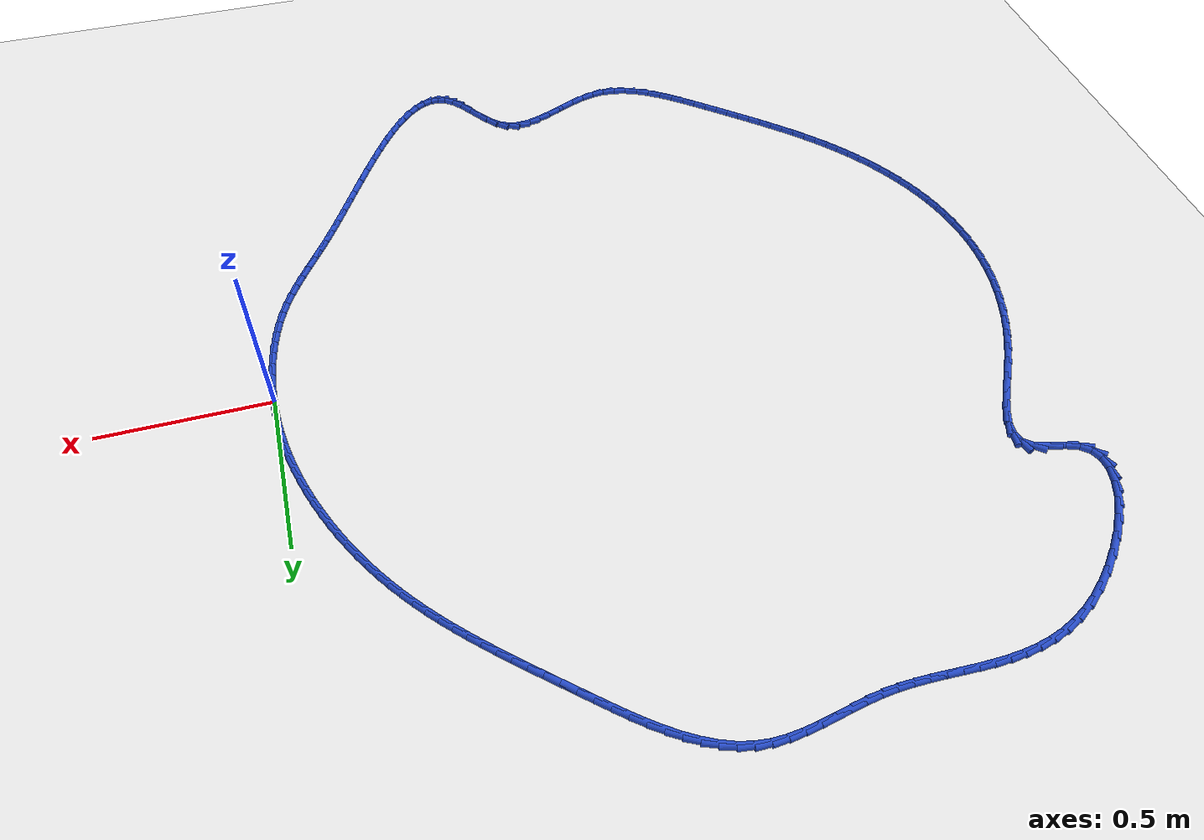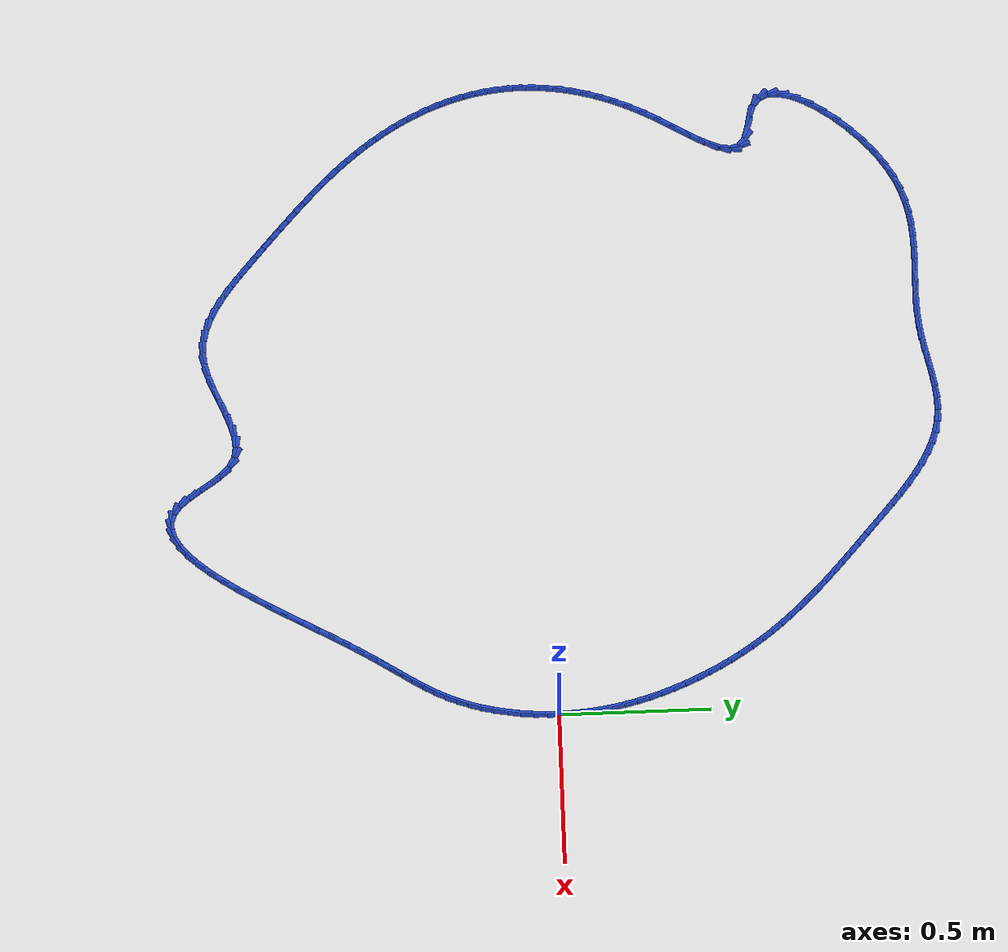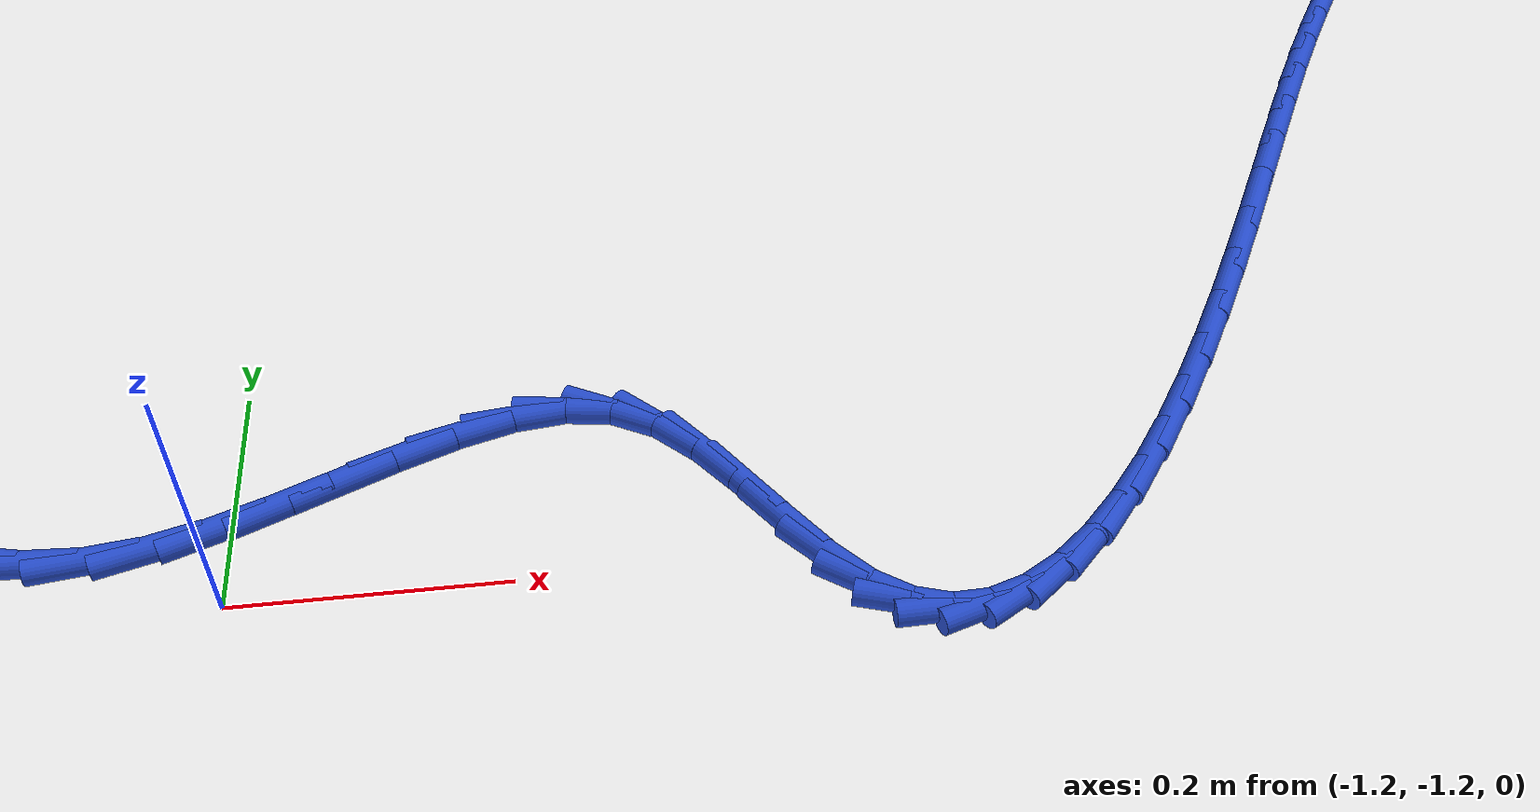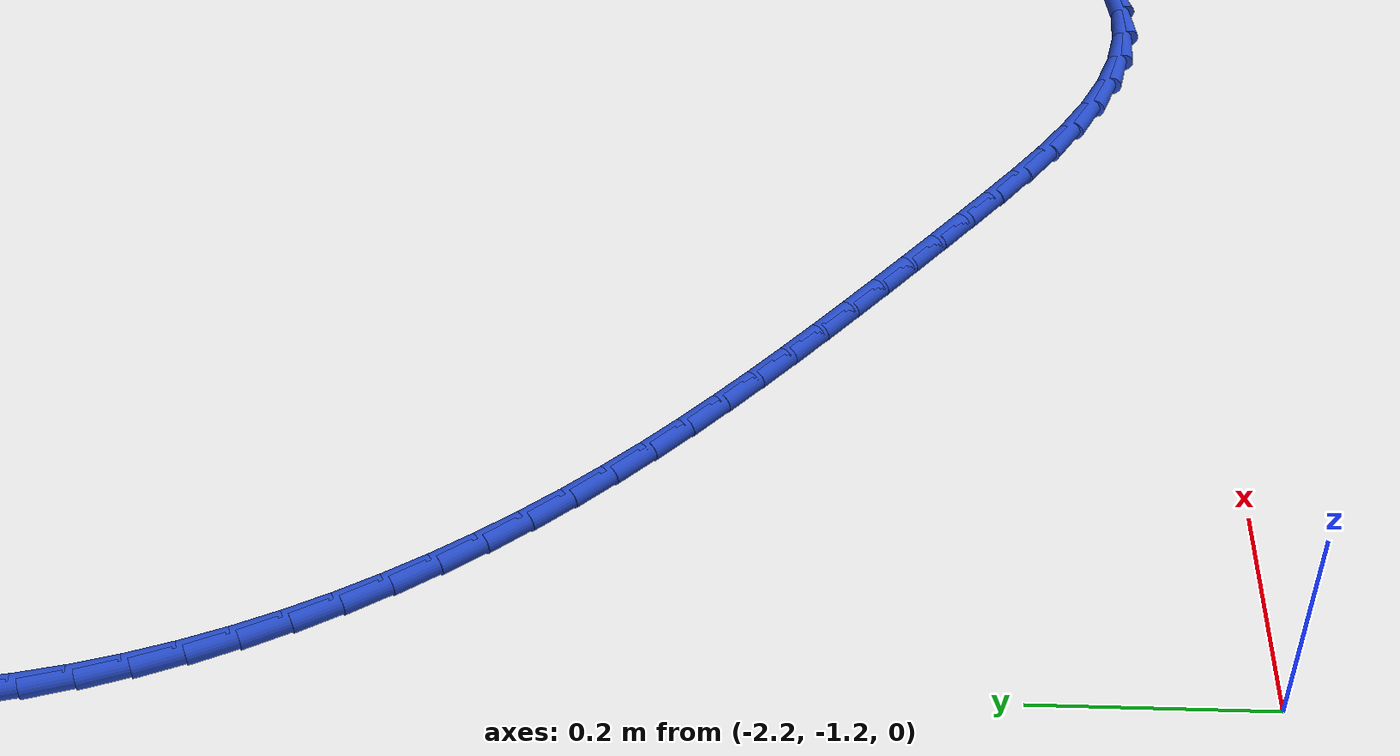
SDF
<sdf version="1.6">
 <world name="default">
  <light name="sun" type="directional">
   <pose>0 0 10 0 -0 0</pose>
   <diffuse>0.8 0.8 0.8 1</diffuse>
   <specular>0.2 0.2 0.2 1</specular>
   <attenuation>
    <range>1000</range>
    <constant>0.9</constant>
    <linear>0.01</linear>
    <quadratic>0.001</quadratic>
   </attenuation>
   <direction>-0.5 0.1 -0.9</direction>
  </light>
  <model name="ground_plane">
   <static>1</static>
   <link name="link">
    <collision name="collision">
     <geometry><plane><normal>0 0 1</normal><size>100 100</size></plane></geometry>
     <surface><friction><ode><mu>100</mu><mu2>50</mu2></ode></friction></surface>
    </collision>
    <visual name="visual">
     <cast_shadows>0</cast_shadows>
     <geometry><plane><normal>0 0 1</normal><size>100 100</size></plane></geometry>
     <material>
      <script><uri>file://media/materials/scripts/gazebo.material</uri><name>Gazebo/WhiteGlow</name></script>
     </material>
    </visual>
   </link>
  </model>
  <gravity>0 0 -9.8</gravity>
  <magnetic_field>6e-06 2.3e-05 -4.2e-05</magnetic_field>
  <atmosphere type="adiabatic"/>
  <physics name="default_physics" default="0" type="ode">
   <max_step_size>0.001</max_step_size>
   <real_time_factor>1</real_time_factor>
   <real_time_update_rate>1000</real_time_update_rate>
  </physics>
  <scene><ambient>0.4 0.4 0.4 1</ambient><background>0.7 0.7 0.7 1</background><shadows>1</shadows></scene>
  <spherical_coordinates>
   <surface_model>EARTH_WGS84</surface_model>
   <latitude_deg>0</latitude_deg>
   <longitude_deg>0</longitude_deg>
   <elevation>0</elevation>
   <heading_deg>0</heading_deg>
  </spherical_coordinates>
  <model name="line">
   <link name="link_0">
    <pose>4.336808689942018e-18 -4.163336342344337e-17 0.01 0 1.57 -1.5419361502482747</pose>
    <collision name="collision">
     <geometry><cylinder><radius>0.01</radius><length>0.08</length></cylinder></geometry>
    </collision>
    <visual name="visual">
     <material>
      <script><name>Gazebo/Blue</name><uri>file://media/materials/scripts/gazebo.material</uri></script>
     </material>
     <geometry><cylinder><radius>0.01</radius><length>0.08</length></cylinder></geometry>
    </visual>
   </link>
   <link name="link_1">
    <pose>-0.001241835568871606 0.0430174350707382 0.01 0 1.57 -1.4992616446270697</pose>
    <collision name="collision">
     <geometry><cylinder><radius>0.01</radius><length>0.08</length></cylinder></geometry>
    </collision>
    <visual name="visual">
     <material>
      <script><name>Gazebo/Blue</name><uri>file://media/materials/scripts/gazebo.material</uri></script>
     </material>
     <geometry><cylinder><radius>0.01</radius><length>0.08</length></cylinder></geometry>
    </visual>
   </link>
   <link name="link_2">
    <pose>-0.0042969841570499896 0.08565319491945013 0.01 0 1.57 -1.457431250953014</pose>
    <collision name="collision">
     <geometry><cylinder><radius>0.01</radius><length>0.08</length></cylinder></geometry>
    </collision>
    <visual name="visual">
     <material>
      <script><name>Gazebo/Blue</name><uri>file://media/materials/scripts/gazebo.material</uri></script>
     </material>
     <geometry><cylinder><radius>0.01</radius><length>0.08</length></cylinder></geometry>
    </visual>
   </link>
   <link name="link_3">
    <pose>-0.009108326376786758 0.12791235886338106 0.01 0 1.57 -1.4166043514242672</pose>
    <collision name="collision">
     <geometry><cylinder><radius>0.01</radius><length>0.08</length></cylinder></geometry>
    </collision>
    <visual name="visual">
     <material>
      <script><name>Gazebo/Blue</name><uri>file://media/materials/scripts/gazebo.material</uri></script>
     </material>
     <geometry><cylinder><radius>0.01</radius><length>0.08</length></cylinder></geometry>
    </visual>
   </link>
   <link name="link_4">
    <pose>-0.015618742840333556 0.16980000621977662 0.01 0 1.57 -1.3769202140500478</pose>
    <collision name="collision">
     <geometry><cylinder><radius>0.01</radius><length>0.08</length></cylinder></geometry>
    </collision>
    <visual name="visual">
     <material>
      <script><name>Gazebo/Blue</name><uri>file://media/materials/scripts/gazebo.material</uri></script>
     </material>
     <geometry><cylinder><radius>0.01</radius><length>0.08</length></cylinder></geometry>
    </visual>
   </link>
   <link name="link_5">
    <pose>-0.023771114159941986 0.21132121630588213 0.01 0 1.57 -1.3384965799225563</pose>
    <collision name="collision">
     <geometry><cylinder><radius>0.01</radius><length>0.08</length></cylinder></geometry>
    </collision>
    <visual name="visual">
     <material>
      <script><name>Gazebo/Blue</name><uri>file://media/materials/scripts/gazebo.material</uri></script>
     </material>
     <geometry><cylinder><radius>0.01</radius><length>0.08</length></cylinder></geometry>
    </visual>
   </link>
   <link name="link_6">
    <pose>-0.03350832094786368 0.2524810684389431 0.01 0 1.57 -1.3014292340319913</pose>
    <collision name="collision">
     <geometry><cylinder><radius>0.01</radius><length>0.08</length></cylinder></geometry>
    </collision>
    <visual name="visual">
     <material>
      <script><name>Gazebo/Blue</name><uri>file://media/materials/scripts/gazebo.material</uri></script>
     </material>
     <geometry><cylinder><radius>0.01</radius><length>0.08</length></cylinder></geometry>
    </visual>
   </link>
   <link name="link_7">
    <pose>-0.04477324381635026 0.293284641936205 0.01 0 1.57 -1.2657924447633824</pose>
    <collision name="collision">
     <geometry><cylinder><radius>0.01</radius><length>0.08</length></cylinder></geometry>
    </collision>
    <visual name="visual">
     <material>
      <script><name>Gazebo/Blue</name><uri>file://media/materials/scripts/gazebo.material</uri></script>
     </material>
     <geometry><cylinder><radius>0.01</radius><length>0.08</length></cylinder></geometry>
    </visual>
   </link>
   <link name="link_8">
    <pose>-0.05750876337765335 0.33373701611491324 0.01 0 1.57 -1.2315676038876533</pose>
    <collision name="collision">
     <geometry><cylinder><radius>0.01</radius><length>0.08</length></cylinder></geometry>
    </collision>
    <visual name="visual">
     <material>
      <script><name>Gazebo/Blue</name><uri>file://media/materials/scripts/gazebo.material</uri></script>
     </material>
     <geometry><cylinder><radius>0.01</radius><length>0.08</length></cylinder></geometry>
    </visual>
   </link>
   <link name="link_9">
    <pose>-0.07165866310954422 0.3738365618099308 0.01 0 1.57 -1.1981974402237439</pose>
    <collision name="collision">
     <geometry><cylinder><radius>0.01</radius><length>0.08</length></cylinder></geometry>
    </collision>
    <visual name="visual">
     <material>
      <script><name>Gazebo/Blue</name><uri>file://media/materials/scripts/gazebo.material</uri></script>
     </material>
     <geometry><cylinder><radius>0.01</radius><length>0.08</length></cylinder></geometry>
    </visual>
   </link>
   <link name="link_10">
    <pose>-0.08717352553571332 0.4135311315023082 0.01 0 1.57 -1.165316105262385</pose>
    <collision name="collision">
     <geometry><cylinder><radius>0.01</radius><length>0.08</length></cylinder></geometry>
    </collision>
    <visual name="visual">
     <material>
      <script><name>Gazebo/Blue</name><uri>file://media/materials/scripts/gazebo.material</uri></script>
     </material>
     <geometry><cylinder><radius>0.01</radius><length>0.08</length></cylinder></geometry>
    </visual>
   </link>
   <link name="link_11">
    <pose>-0.10400703066744613 0.4527455626830358 0.01 0 1.57 -1.132789994508953</pose>
    <collision name="collision">
     <geometry><cylinder><radius>0.01</radius><length>0.08</length></cylinder></geometry>
    </collision>
    <visual name="visual">
     <material>
      <script><name>Gazebo/Blue</name><uri>file://media/materials/scripts/gazebo.material</uri></script>
     </material>
     <geometry><cylinder><radius>0.01</radius><length>0.08</length></cylinder></geometry>
    </visual>
   </link>
   <link name="link_12">
    <pose>-0.12211287423397113 0.49140457605545124 0.01 0 1.57 -1.1004872258329634</pose>
    <collision name="collision">
     <geometry><cylinder><radius>0.01</radius><length>0.08</length></cylinder></geometry>
    </collision>
    <visual name="visual">
     <material>
      <script><name>Gazebo/Blue</name><uri>file://media/materials/scripts/gazebo.material</uri></script>
     </material>
     <geometry><cylinder><radius>0.01</radius><length>0.08</length></cylinder></geometry>
    </visual>
   </link>
   <link name="link_13">
    <pose>-0.14144475196451692 0.5294328923228926 0.01 0 1.57 -1.0682757105273728</pose>
    <collision name="collision">
     <geometry><cylinder><radius>0.01</radius><length>0.08</length></cylinder></geometry>
    </collision>
    <visual name="visual">
     <material>
      <script><name>Gazebo/Blue</name><uri>file://media/materials/scripts/gazebo.material</uri></script>
     </material>
     <geometry><cylinder><radius>0.01</radius><length>0.08</length></cylinder></geometry>
    </visual>
   </link>
   <link name="link_14">
    <pose>-0.16195635958831195 0.5667552321886977 0.01 0 1.57 -1.036022394601772</pose>
    <collision name="collision">
     <geometry><cylinder><radius>0.01</radius><length>0.08</length></cylinder></geometry>
    </collision>
    <visual name="visual">
     <material>
      <script><name>Gazebo/Blue</name><uri>file://media/materials/scripts/gazebo.material</uri></script>
     </material>
     <geometry><cylinder><radius>0.01</radius><length>0.08</length></cylinder></geometry>
    </visual>
   </link>
   <link name="link_15">
    <pose>-0.18360139283458476 0.6032963163562044 0.01 0 1.57 -1.0035924352598167</pose>
    <collision name="collision">
     <geometry><cylinder><radius>0.01</radius><length>0.08</length></cylinder></geometry>
    </collision>
    <visual name="visual">
     <material>
      <script><name>Gazebo/Blue</name><uri>file://media/materials/scripts/gazebo.material</uri></script>
     </material>
     <geometry><cylinder><radius>0.01</radius><length>0.08</length></cylinder></geometry>
    </visual>
   </link>
   <link name="link_16">
    <pose>-0.206333547432564 0.6389808655287509 0.01 0 1.57 -0.9708483380710354</pose>
    <collision name="collision">
     <geometry><cylinder><radius>0.01</radius><length>0.08</length></cylinder></geometry>
    </collision>
    <visual name="visual">
     <material>
      <script><name>Gazebo/Blue</name><uri>file://media/materials/scripts/gazebo.material</uri></script>
     </material>
     <geometry><cylinder><radius>0.01</radius><length>0.08</length></cylinder></geometry>
    </visual>
   </link>
   <link name="link_17">
    <pose>-0.23010651911147798 0.6737336004096743 0.01 0 1.57 -0.9376976790625575</pose>
    <collision name="collision">
     <geometry><cylinder><radius>0.01</radius><length>0.08</length></cylinder></geometry>
    </collision>
    <visual name="visual">
     <material>
      <script><name>Gazebo/Blue</name><uri>file://media/materials/scripts/gazebo.material</uri></script>
     </material>
     <geometry><cylinder><radius>0.01</radius><length>0.08</length></cylinder></geometry>
    </visual>
   </link>
   <link name="link_18">
    <pose>-0.25487396065937173 0.7074826215023428 0.01 0 1.57 -0.9053284936645193</pose>
    <collision name="collision">
     <geometry><cylinder><radius>0.01</radius><length>0.08</length></cylinder></geometry>
    </collision>
    <visual name="visual">
     <material>
      <script><name>Gazebo/Blue</name><uri>file://media/materials/scripts/gazebo.material</uri></script>
     </material>
     <geometry><cylinder><radius>0.01</radius><length>0.08</length></cylinder></geometry>
    </visual>
   </link>
   <link name="link_19">
    <pose>-0.28058840843976807 0.7402439004701922 0.01 0 1.57 -0.8752572905753323</pose>
    <collision name="collision">
     <geometry><cylinder><radius>0.01</radius><length>0.08</length></cylinder></geometry>
    </collision>
    <visual name="visual">
     <material>
      <script><name>Gazebo/Blue</name><uri>file://media/materials/scripts/gazebo.material</uri></script>
     </material>
     <geometry><cylinder><radius>0.01</radius><length>0.08</length></cylinder></geometry>
    </visual>
   </link>
   <link name="link_20">
    <pose>-0.30720120578513094 0.7721273096579496 0.01 0 1.57 -0.8477517682803674</pose>
    <collision name="collision">
     <geometry><cylinder><radius>0.01</radius><length>0.08</length></cylinder></geometry>
    </collision>
    <visual name="visual">
     <material>
      <script><name>Gazebo/Blue</name><uri>file://media/materials/scripts/gazebo.material</uri></script>
     </material>
     <geometry><cylinder><radius>0.01</radius><length>0.08</length></cylinder></geometry>
    </visual>
   </link>
   <link name="link_21">
    <pose>-0.33466363774427516 0.8032473087798585 0.01 0 1.57 -0.8229682808153514</pose>
    <collision name="collision">
     <geometry><cylinder><radius>0.01</radius><length>0.08</length></cylinder></geometry>
    </collision>
    <visual name="visual">
     <material>
      <script><name>Gazebo/Blue</name><uri>file://media/materials/scripts/gazebo.material</uri></script>
     </material>
     <geometry><cylinder><radius>0.01</radius><length>0.08</length></cylinder></geometry>
    </visual>
   </link>
   <link name="link_22">
    <pose>-0.3629269893660159 0.8337183575501643 0.01 0 1.57 -0.8010197723613873</pose>
    <collision name="collision">
     <geometry><cylinder><radius>0.01</radius><length>0.08</length></cylinder></geometry>
    </collision>
    <visual name="visual">
     <material>
      <script><name>Gazebo/Blue</name><uri>file://media/materials/scripts/gazebo.material</uri></script>
     </material>
     <geometry><cylinder><radius>0.01</radius><length>0.08</length></cylinder></geometry>
    </visual>
   </link>
   <link name="link_23">
    <pose>-0.39194254569916803 0.8636549156831111 0.01 0 1.57 -0.7819793040330866</pose>
    <collision name="collision">
     <geometry><cylinder><radius>0.01</radius><length>0.08</length></cylinder></geometry>
    </collision>
    <visual name="visual">
     <material>
      <script><name>Gazebo/Blue</name><uri>file://media/materials/scripts/gazebo.material</uri></script>
     </material>
     <geometry><cylinder><radius>0.01</radius><length>0.08</length></cylinder></geometry>
    </visual>
   </link>
   <link name="link_24">
    <pose>-0.4216615917925466 0.893171442892944 0.01 0 1.57 -0.7658844997004426</pose>
    <collision name="collision">
     <geometry><cylinder><radius>0.01</radius><length>0.08</length></cylinder></geometry>
    </collision>
    <visual name="visual">
     <material>
      <script><name>Gazebo/Blue</name><uri>file://media/materials/scripts/gazebo.material</uri></script>
     </material>
     <geometry><cylinder><radius>0.01</radius><length>0.08</length></cylinder></geometry>
    </visual>
   </link>
   <link name="link_25">
    <pose>-0.4520354126949668 0.9223823988939074 0.01 0 1.57 -0.7527423559418361</pose>
    <collision name="collision">
     <geometry><cylinder><radius>0.01</radius><length>0.08</length></cylinder></geometry>
    </collision>
    <visual name="visual">
     <material>
      <script><name>Gazebo/Blue</name><uri>file://media/materials/scripts/gazebo.material</uri></script>
     </material>
     <geometry><cylinder><radius>0.01</radius><length>0.08</length></cylinder></geometry>
    </visual>
   </link>
   <link name="link_26">
    <pose>-0.4830152934552434 0.9514022434002459 0.01 0 1.57 -0.7425339751263574</pose>
    <collision name="collision">
     <geometry><cylinder><radius>0.01</radius><length>0.08</length></cylinder></geometry>
    </collision>
    <visual name="visual">
     <material>
      <script><name>Gazebo/Blue</name><uri>file://media/materials/scripts/gazebo.material</uri></script>
     </material>
     <geometry><cylinder><radius>0.01</radius><length>0.08</length></cylinder></geometry>
    </visual>
   </link>
   <link name="link_27">
    <pose>-0.5145525191221915 0.9803454361262041 0.01 0 1.57 -0.7352189091202924</pose>
    <collision name="collision">
     <geometry><cylinder><radius>0.01</radius><length>0.08</length></cylinder></geometry>
    </collision>
    <visual name="visual">
     <material>
      <script><name>Gazebo/Blue</name><uri>file://media/materials/scripts/gazebo.material</uri></script>
     </material>
     <geometry><cylinder><radius>0.01</radius><length>0.08</length></cylinder></geometry>
    </visual>
   </link>
   <link name="link_28">
    <pose>-0.5465983747446262 1.0093264367860266 0.01 0 1.57 -0.7307389229446388</pose>
    <collision name="collision">
     <geometry><cylinder><radius>0.01</radius><length>0.08</length></cylinder></geometry>
    </collision>
    <visual name="visual">
     <material>
      <script><name>Gazebo/Blue</name><uri>file://media/materials/scripts/gazebo.material</uri></script>
     </material>
     <geometry><cylinder><radius>0.01</radius><length>0.08</length></cylinder></geometry>
    </visual>
   </link>
   <link name="link_29">
    <pose>-0.5791041453713623 1.0384597050939584 0.01 0 1.57 -0.7290210908616706</pose>
    <collision name="collision">
     <geometry><cylinder><radius>0.01</radius><length>0.08</length></cylinder></geometry>
    </collision>
    <visual name="visual">
     <material>
      <script><name>Gazebo/Blue</name><uri>file://media/materials/scripts/gazebo.material</uri></script>
     </material>
     <geometry><cylinder><radius>0.01</radius><length>0.08</length></cylinder></geometry>
    </visual>
   </link>
   <link name="link_30">
    <pose>-0.6120211160512152 1.0678597007642436 0.01 0 1.57 -0.7296109554559106</pose>
    <collision name="collision">
     <geometry><cylinder><radius>0.01</radius><length>0.08</length></cylinder></geometry>
    </collision>
    <visual name="visual">
     <material>
      <script><name>Gazebo/Blue</name><uri>file://media/materials/scripts/gazebo.material</uri></script>
     </material>
     <geometry><cylinder><radius>0.01</radius><length>0.08</length></cylinder></geometry>
    </visual>
   </link>
   <link name="link_31">
    <pose>-0.6453037108062956 1.097621567841827 0.01 0 1.57 -0.7257256915192237</pose>
    <collision name="collision">
     <geometry><cylinder><radius>0.01</radius><length>0.08</length></cylinder></geometry>
    </collision>
    <visual name="visual">
     <material>
      <script><name>Gazebo/Blue</name><uri>file://media/materials/scripts/gazebo.material</uri></script>
     </material>
     <geometry><cylinder><radius>0.01</radius><length>0.08</length></cylinder></geometry>
    </visual>
   </link>
   <link name="link_32">
    <pose>-0.6789638703955015 1.1274865211845937 0.01 0 1.57 -0.7115037725137986</pose>
    <collision name="collision">
     <geometry><cylinder><radius>0.01</radius><length>0.08</length></cylinder></geometry>
    </collision>
    <visual name="visual">
     <material>
      <script><name>Gazebo/Blue</name><uri>file://media/materials/scripts/gazebo.material</uri></script>
     </material>
     <geometry><cylinder><radius>0.01</radius><length>0.08</length></cylinder></geometry>
    </visual>
   </link>
   <link name="link_33">
    <pose>-0.7130639150809771 1.156885765423402 0.01 0 1.57 -0.686454915482505</pose>
    <collision name="collision">
     <geometry><cylinder><radius>0.01</radius><length>0.08</length></cylinder></geometry>
    </collision>
    <visual name="visual">
     <material>
      <script><name>Gazebo/Blue</name><uri>file://media/materials/scripts/gazebo.material</uri></script>
     </material>
     <geometry><cylinder><radius>0.01</radius><length>0.08</length></cylinder></geometry>
    </visual>
   </link>
   <link name="link_34">
    <pose>-0.7476678687918933 1.1852400216756258 0.01 0 1.57 -0.6498588343215467</pose>
    <collision name="collision">
     <geometry><cylinder><radius>0.01</radius><length>0.08</length></cylinder></geometry>
    </collision>
    <visual name="visual">
     <material>
      <script><name>Gazebo/Blue</name><uri>file://media/materials/scripts/gazebo.material</uri></script>
     </material>
     <geometry><cylinder><radius>0.01</radius><length>0.08</length></cylinder></geometry>
    </visual>
   </link>
   <link name="link_35">
    <pose>-0.7828397554574216 1.2119700110586393 0.01 0 1.57 -0.6006031645662075</pose>
    <collision name="collision">
     <geometry><cylinder><radius>0.01</radius><length>0.08</length></cylinder></geometry>
    </collision>
    <visual name="visual">
     <material>
      <script><name>Gazebo/Blue</name><uri>file://media/materials/scripts/gazebo.material</uri></script>
     </material>
     <geometry><cylinder><radius>0.01</radius><length>0.08</length></cylinder></geometry>
    </visual>
   </link>
   <link name="link_36">
    <pose>-0.8186435990067328 1.236496454689817 0.01 0 1.57 -0.5372653583464293</pose>
    <collision name="collision">
     <geometry><cylinder><radius>0.01</radius><length>0.08</length></cylinder></geometry>
    </collision>
    <visual name="visual">
     <material>
      <script><name>Gazebo/Blue</name><uri>file://media/materials/scripts/gazebo.material</uri></script>
     </material>
     <geometry><cylinder><radius>0.01</radius><length>0.08</length></cylinder></geometry>
    </visual>
   </link>
   <link name="link_37">
    <pose>-0.8551434233689977 1.2582400736865322 0.01 0 1.57 -0.45830006181834854</pose>
    <collision name="collision">
     <geometry><cylinder><radius>0.01</radius><length>0.08</length></cylinder></geometry>
    </collision>
    <visual name="visual">
     <material>
      <script><name>Gazebo/Blue</name><uri>file://media/materials/scripts/gazebo.material</uri></script>
     </material>
     <geometry><cylinder><radius>0.01</radius><length>0.08</length></cylinder></geometry>
    </visual>
   </link>
   <link name="link_38">
    <pose>-0.8924032524733878 1.276621589166159 0.01 0 1.57 -0.3624187092340209</pose>
    <collision name="collision">
     <geometry><cylinder><radius>0.01</radius><length>0.08</length></cylinder></geometry>
    </collision>
    <visual name="visual">
     <material>
      <script><name>Gazebo/Blue</name><uri>file://media/materials/scripts/gazebo.material</uri></script>
     </material>
     <geometry><cylinder><radius>0.01</radius><length>0.08</length></cylinder></geometry>
    </visual>
   </link>
   <link name="link_39">
    <pose>-0.9304871102490737 1.2910617222460712 0.01 0 1.57 -0.24923645722205326</pose>
    <collision name="collision">
     <geometry><cylinder><radius>0.01</radius><length>0.08</length></cylinder></geometry>
    </collision>
    <visual name="visual">
     <material>
      <script><name>Gazebo/Blue</name><uri>file://media/materials/scripts/gazebo.material</uri></script>
     </material>
     <geometry><cylinder><radius>0.01</radius><length>0.08</length></cylinder></geometry>
    </visual>
   </link>
   <link name="link_40">
    <pose>-0.9694590206252272 1.3009811940436438 0.01 0 1.57 -0.12096045619981854</pose>
    <collision name="collision">
     <geometry><cylinder><radius>0.01</radius><length>0.08</length></cylinder></geometry>
    </collision>
    <visual name="visual">
     <material>
      <script><name>Gazebo/Blue</name><uri>file://media/materials/scripts/gazebo.material</uri></script>
     </material>
     <geometry><cylinder><radius>0.01</radius><length>0.08</length></cylinder></geometry>
    </visual>
   </link>
   <link name="link_41">
    <pose>-1.009378238541521 1.3058335295089432 0.01 0 1.57 -0.0005305506945611249</pose>
    <collision name="collision">
     <geometry><cylinder><radius>0.01</radius><length>0.08</length></cylinder></geometry>
    </collision>
    <visual name="visual">
     <material>
      <script><name>Gazebo/Blue</name><uri>file://media/materials/scripts/gazebo.material</uri></script>
     </material>
     <geometry><cylinder><radius>0.01</radius><length>0.08</length></cylinder></geometry>
    </visual>
   </link>
   <link name="link_42">
    <pose>-1.0501901975151366 1.3058551823241547 0.01 0 1.57 0.09060492197023447</pose>
    <collision name="collision">
     <geometry><cylinder><radius>0.01</radius><length>0.08</length></cylinder></geometry>
    </collision>
    <visual name="visual">
     <material>
      <script><name>Gazebo/Blue</name><uri>file://media/materials/scripts/gazebo.material</uri></script>
     </material>
     <geometry><cylinder><radius>0.01</radius><length>0.08</length></cylinder></geometry>
    </visual>
   </link>
   <link name="link_43">
    <pose>-1.0917241640870925 1.3020816689609378 0.01 0 1.57 0.15318985053201506</pose>
    <collision name="collision">
     <geometry><cylinder><radius>0.01</radius><length>0.08</length></cylinder></geometry>
    </collision>
    <visual name="visual">
     <material>
      <script><name>Gazebo/Blue</name><uri>file://media/materials/scripts/gazebo.material</uri></script>
     </material>
     <geometry><cylinder><radius>0.01</radius><length>0.08</length></cylinder></geometry>
    </visual>
   </link>
   <link name="link_44">
    <pose>-1.133804166636989 1.2955845369559973 0.01 0 1.57 0.189664067207355</pose>
    <collision name="collision">
     <geometry><cylinder><radius>0.01</radius><length>0.08</length></cylinder></geometry>
    </collision>
    <visual name="visual">
     <material>
      <script><name>Gazebo/Blue</name><uri>file://media/materials/scripts/gazebo.material</uri></script>
     </material>
     <geometry><cylinder><radius>0.01</radius><length>0.08</length></cylinder></geometry>
    </visual>
   </link>
   <link name="link_45">
    <pose>-1.1762542335444268 1.2874353338460396 0.01 0 1.57 0.2019211940629193</pose>
    <collision name="collision">
     <geometry><cylinder><radius>0.01</radius><length>0.08</length></cylinder></geometry>
    </collision>
    <visual name="visual">
     <material>
      <script><name>Gazebo/Blue</name><uri>file://media/materials/scripts/gazebo.material</uri></script>
     </material>
     <geometry><cylinder><radius>0.01</radius><length>0.08</length></cylinder></geometry>
    </visual>
   </link>
   <link name="link_46">
    <pose>-1.2188983931890083 1.2787056071677696 0.01 0 1.57 0.19076615344599673</pose>
    <collision name="collision">
     <geometry><cylinder><radius>0.01</radius><length>0.08</length></cylinder></geometry>
    </collision>
    <visual name="visual">
     <material>
      <script><name>Gazebo/Blue</name><uri>file://media/materials/scripts/gazebo.material</uri></script>
     </material>
     <geometry><cylinder><radius>0.01</radius><length>0.08</length></cylinder></geometry>
    </visual>
   </link>
   <link name="link_47">
    <pose>-1.2615606739503331 1.2704669044578945 0.01 0 1.57 0.1557961887127019</pose>
    <collision name="collision">
     <geometry><cylinder><radius>0.01</radius><length>0.08</length></cylinder></geometry>
    </collision>
    <visual name="visual">
     <material>
      <script><name>Gazebo/Blue</name><uri>file://media/materials/scripts/gazebo.material</uri></script>
     </material>
     <geometry><cylinder><radius>0.01</radius><length>0.08</length></cylinder></geometry>
    </visual>
   </link>
   <link name="link_48">
    <pose>-1.3040651042080018 1.2637907732531186 0.01 0 1.57 0.09903551278149271</pose>
    <collision name="collision">
     <geometry><cylinder><radius>0.01</radius><length>0.08</length></cylinder></geometry>
    </collision>
    <visual name="visual">
     <material>
      <script><name>Gazebo/Blue</name><uri>file://media/materials/scripts/gazebo.material</uri></script>
     </material>
     <geometry><cylinder><radius>0.01</radius><length>0.08</length></cylinder></geometry>
    </visual>
   </link>
   <link name="link_49">
    <pose>-1.3462566678803733 1.259598595467283 0.01 0 1.57 0.04440557780511268</pose>
    <collision name="collision">
     <geometry><cylinder><radius>0.01</radius><length>0.08</length></cylinder></geometry>
    </collision>
    <visual name="visual">
     <material>
      <script><name>Gazebo/Blue</name><uri>file://media/materials/scripts/gazebo.material</uri></script>
     </material>
     <geometry><cylinder><radius>0.01</radius><length>0.08</length></cylinder></geometry>
    </visual>
   </link>
   <link name="link_50">
    <pose>-1.3881301969986182 1.257737954079364 0.01 0 1.57 0.0035818226013987716</pose>
    <collision name="collision">
     <geometry><cylinder><radius>0.01</radius><length>0.08</length></cylinder></geometry>
    </collision>
    <visual name="visual">
     <material>
      <script><name>Gazebo/Blue</name><uri>file://media/materials/scripts/gazebo.material</uri></script>
     </material>
     <geometry><cylinder><radius>0.01</radius><length>0.08</length></cylinder></geometry>
    </visual>
   </link>
   <link name="link_51">
    <pose>-1.4297457683224306 1.257588893847972 0.01 0 1.57 -0.022707000567354595</pose>
    <collision name="collision">
     <geometry><cylinder><radius>0.01</radius><length>0.08</length></cylinder></geometry>
    </collision>
    <visual name="visual">
     <material>
      <script><name>Gazebo/Blue</name><uri>file://media/materials/scripts/gazebo.material</uri></script>
     </material>
     <geometry><cylinder><radius>0.01</radius><length>0.08</length></cylinder></geometry>
    </visual>
   </link>
   <link name="link_52">
    <pose>-1.4711637274382843 1.2585295331416808 0.01 0 1.57 -0.03410579986759467</pose>
    <collision name="collision">
     <geometry><cylinder><radius>0.01</radius><length>0.08</length></cylinder></geometry>
    </collision>
    <visual name="visual">
     <material>
      <script><name>Gazebo/Blue</name><uri>file://media/materials/scripts/gazebo.material</uri></script>
     </material>
     <geometry><cylinder><radius>0.01</radius><length>0.08</length></cylinder></geometry>
    </visual>
   </link>
   <link name="link_53">
    <pose>-1.5124444199326534 1.2599379903290653 0.01 0 1.57 -0.030434256133795114</pose>
    <collision name="collision">
     <geometry><cylinder><radius>0.01</radius><length>0.08</length></cylinder></geometry>
    </collision>
    <visual name="visual">
     <material>
      <script><name>Gazebo/Blue</name><uri>file://media/materials/scripts/gazebo.material</uri></script>
     </material>
     <geometry><cylinder><radius>0.01</radius><length>0.08</length></cylinder></geometry>
    </visual>
   </link>
   <link name="link_54">
    <pose>-1.5536481913920124 1.2611923837787014 0.01 0 1.57 -0.011615905128925012</pose>
    <collision name="collision">
     <geometry><cylinder><radius>0.01</radius><length>0.08</length></cylinder></geometry>
    </collision>
    <visual name="visual">
     <material>
      <script><name>Gazebo/Blue</name><uri>file://media/materials/scripts/gazebo.material</uri></script>
     </material>
     <geometry><cylinder><radius>0.01</radius><length>0.08</length></cylinder></geometry>
    </visual>
   </link>
   <link name="link_55">
    <pose>-1.5948353874028358 1.2616708318591636 0.01 0 1.57 0.02229456827886335</pose>
    <collision name="collision">
     <geometry><cylinder><radius>0.01</radius><length>0.08</length></cylinder></geometry>
    </collision>
    <visual name="visual">
     <material>
      <script><name>Gazebo/Blue</name><uri>file://media/materials/scripts/gazebo.material</uri></script>
     </material>
     <geometry><cylinder><radius>0.01</radius><length>0.08</length></cylinder></geometry>
    </visual>
   </link>
   <link name="link_56">
    <pose>-1.6360663535515962 1.2607514529390267 0.01 0 1.57 0.0709844827161357</pose>
    <collision name="collision">
     <geometry><cylinder><radius>0.01</radius><length>0.08</length></cylinder></geometry>
    </collision>
    <visual name="visual">
     <material>
      <script><name>Gazebo/Blue</name><uri>file://media/materials/scripts/gazebo.material</uri></script>
     </material>
     <geometry><cylinder><radius>0.01</radius><length>0.08</length></cylinder></geometry>
    </visual>
   </link>
   <link name="link_57">
    <pose>-1.6774014354247688 1.2578123653868658 0.01 0 1.57 0.1336737220131901</pose>
    <collision name="collision">
     <geometry><cylinder><radius>0.01</radius><length>0.08</length></cylinder></geometry>
    </collision>
    <visual name="visual">
     <material>
      <script><name>Gazebo/Blue</name><uri>file://media/materials/scripts/gazebo.material</uri></script>
     </material>
     <geometry><cylinder><radius>0.01</radius><length>0.08</length></cylinder></geometry>
    </visual>
   </link>
   <link name="link_58">
    <pose>-1.7189009786088283 1.2522316875712565 0.01 0 1.57 0.20887454952535145</pose>
    <collision name="collision">
     <geometry><cylinder><radius>0.01</radius><length>0.08</length></cylinder></geometry>
    </collision>
    <visual name="visual">
     <material>
      <script><name>Gazebo/Blue</name><uri>file://media/materials/scripts/gazebo.material</uri></script>
     </material>
     <geometry><cylinder><radius>0.01</radius><length>0.08</length></cylinder></geometry>
    </visual>
   </link>
   <link name="link_59">
    <pose>-1.7606253286902478 1.2433875378607735 0.01 0 1.57 0.2942204142676285</pose>
    <collision name="collision">
     <geometry><cylinder><radius>0.01</radius><length>0.08</length></cylinder></geometry>
    </collision>
    <visual name="visual">
     <material>
      <script><name>Gazebo/Blue</name><uri>file://media/materials/scripts/gazebo.material</uri></script>
     </material>
     <geometry><cylinder><radius>0.01</radius><length>0.08</length></cylinder></geometry>
    </visual>
   </link>
   <link name="link_60">
    <pose>-1.802634831255502 1.230658034623992 0.01 0 1.57 0.3864908733762169</pose>
    <collision name="collision">
     <geometry><cylinder><radius>0.01</radius><length>0.08</length></cylinder></geometry>
    </collision>
    <visual name="visual">
     <material>
      <script><name>Gazebo/Blue</name><uri>file://media/materials/scripts/gazebo.material</uri></script>
     </material>
     <geometry><cylinder><radius>0.01</radius><length>0.08</length></cylinder></geometry>
    </visual>
   </link>
   <link name="link_61">
    <pose>-1.8449898318910651 1.213421296229487 0.01 0 1.57 0.4819133588384118</pose>
    <collision name="collision">
     <geometry><cylinder><radius>0.01</radius><length>0.08</length></cylinder></geometry>
    </collision>
    <visual name="visual">
     <material>
      <script><name>Gazebo/Blue</name><uri>file://media/materials/scripts/gazebo.material</uri></script>
     </material>
     <geometry><cylinder><radius>0.01</radius><length>0.08</length></cylinder></geometry>
    </visual>
   </link>
   <link name="link_62">
    <pose>-1.8877506761834104 1.1910554410458334 0.01 0 1.57 0.5766887256138101</pose>
    <collision name="collision">
     <geometry><cylinder><radius>0.01</radius><length>0.08</length></cylinder></geometry>
    </collision>
    <visual name="visual">
     <material>
      <script><name>Gazebo/Blue</name><uri>file://media/materials/scripts/gazebo.material</uri></script>
     </material>
     <geometry><cylinder><radius>0.01</radius><length>0.08</length></cylinder></geometry>
    </visual>
   </link>
   <link name="link_63">
    <pose>-1.9309777093081482 1.1629385880186054 0.01 0 1.57 0.665396361926923</pose>
    <collision name="collision">
     <geometry><cylinder><radius>0.01</radius><length>0.08</length></cylinder></geometry>
    </collision>
    <visual name="visual">
     <material>
      <script><name>Gazebo/Blue</name><uri>file://media/materials/scripts/gazebo.material</uri></script>
     </material>
     <geometry><cylinder><radius>0.01</radius><length>0.08</length></cylinder></geometry>
    </visual>
   </link>
   <link name="link_64">
    <pose>-1.9744852148377674 1.1287944126287217 0.01 0 1.57 0.7421518401114799</pose>
    <collision name="collision">
     <geometry><cylinder><radius>0.01</radius><length>0.08</length></cylinder></geometry>
    </collision>
    <visual name="visual">
     <material>
      <script><name>Gazebo/Blue</name><uri>file://media/materials/scripts/gazebo.material</uri></script>
     </material>
     <geometry><cylinder><radius>0.01</radius><length>0.08</length></cylinder></geometry>
    </visual>
   </link>
   <link name="link_65">
    <pose>-2.0171380439547075 1.0896799254369893 0.01 0 1.57 0.8127211256288346</pose>
    <collision name="collision">
     <geometry><cylinder><radius>0.01</radius><length>0.08</length></cylinder></geometry>
    </collision>
    <visual name="visual">
     <material>
      <script><name>Gazebo/Blue</name><uri>file://media/materials/scripts/gazebo.material</uri></script>
     </material>
     <geometry><cylinder><radius>0.01</radius><length>0.08</length></cylinder></geometry>
    </visual>
   </link>
   <link name="link_66">
    <pose>-2.05757208751583 1.0469736773657985 0.01 0 1.57 0.8837498525271367</pose>
    <collision name="collision">
     <geometry><cylinder><radius>0.01</radius><length>0.08</length></cylinder></geometry>
    </collision>
    <visual name="visual">
     <material>
      <script><name>Gazebo/Blue</name><uri>file://media/materials/scripts/gazebo.material</uri></script>
     </material>
     <geometry><cylinder><radius>0.01</radius><length>0.08</length></cylinder></geometry>
    </visual>
   </link>
   <link name="link_67">
    <pose>-2.0944232363779944 1.0020542193375408 0.01 0 1.57 0.9618876954355615</pose>
    <collision name="collision">
     <geometry><cylinder><radius>0.01</radius><length>0.08</length></cylinder></geometry>
    </collision>
    <visual name="visual">
     <material>
      <script><name>Gazebo/Blue</name><uri>file://media/materials/scripts/gazebo.material</uri></script>
     </material>
     <geometry><cylinder><radius>0.01</radius><length>0.08</length></cylinder></geometry>
    </visual>
   </link>
   <link name="link_68">
    <pose>-2.126327381398061 0.9563001022746064 0.01 0 1.57 1.0556843361926722</pose>
    <collision name="collision">
     <geometry><cylinder><radius>0.01</radius><length>0.08</length></cylinder></geometry>
    </collision>
    <visual name="visual">
     <material>
      <script><name>Gazebo/Blue</name><uri>file://media/materials/scripts/gazebo.material</uri></script>
     </material>
     <geometry><cylinder><radius>0.01</radius><length>0.08</length></cylinder></geometry>
    </visual>
   </link>
   <link name="link_69">
    <pose>-2.151920413432891 0.9110898770993847 0.01 0 1.57 1.178345258063743</pose>
    <collision name="collision">
     <geometry><cylinder><radius>0.01</radius><length>0.08</length></cylinder></geometry>
    </collision>
    <visual name="visual">
     <material>
      <script><name>Gazebo/Blue</name><uri>file://media/materials/scripts/gazebo.material</uri></script>
     </material>
     <geometry><cylinder><radius>0.01</radius><length>0.08</length></cylinder></geometry>
    </visual>
   </link>
   <link name="link_70">
    <pose>-2.1698382233393447 0.8678020947342681 0.01 0 1.57 1.352305513260158</pose>
    <collision name="collision">
     <geometry><cylinder><radius>0.01</radius><length>0.08</length></cylinder></geometry>
    </collision>
    <visual name="visual">
     <material>
      <script><name>Gazebo/Blue</name><uri>file://media/materials/scripts/gazebo.material</uri></script>
     </material>
     <geometry><cylinder><radius>0.01</radius><length>0.08</length></cylinder></geometry>
    </visual>
   </link>
   <link name="link_71">
    <pose>-2.1787167019742815 0.8278153061016456 0.01 0 1.57 -1.527631967111814</pose>
    <collision name="collision">
     <geometry><cylinder><radius>0.01</radius><length>0.08</length></cylinder></geometry>
    </collision>
    <visual name="visual">
     <material>
      <script><name>Gazebo/Blue</name><uri>file://media/materials/scripts/gazebo.material</uri></script>
     </material>
     <geometry><cylinder><radius>0.01</radius><length>0.08</length></cylinder></geometry>
    </visual>
   </link>
   <link name="link_72">
    <pose>-2.177191740194563 0.7925080621239089 0.01 0 1.57 -1.1442412629792813</pose>
    <collision name="collision">
     <geometry><cylinder><radius>0.01</radius><length>0.08</length></cylinder></geometry>
    </collision>
    <visual name="visual">
     <material>
      <script><name>Gazebo/Blue</name><uri>file://media/materials/scripts/gazebo.material</uri></script>
     </material>
     <geometry><cylinder><radius>0.01</radius><length>0.08</length></cylinder></geometry>
    </visual>
   </link>
   <link name="link_73">
    <pose>-2.1638992288570504 0.7632589137234482 0.01 0 1.57 -0.6900828399752187</pose>
    <collision name="collision">
     <geometry><cylinder><radius>0.01</radius><length>0.08</length></cylinder></geometry>
    </collision>
    <visual name="visual">
     <material>
      <script><name>Gazebo/Blue</name><uri>file://media/materials/scripts/gazebo.material</uri></script>
     </material>
     <geometry><cylinder><radius>0.01</radius><length>0.08</length></cylinder></geometry>
    </visual>
   </link>
   <link name="link_74">
    <pose>-2.1374750588186027 0.7414464118226538 0.01 0 1.57 -0.33874433907926044</pose>
    <collision name="collision">
     <geometry><cylinder><radius>0.01</radius><length>0.08</length></cylinder></geometry>
    </collision>
    <visual name="visual">
     <material>
      <script><name>Gazebo/Blue</name><uri>file://media/materials/scripts/gazebo.material</uri></script>
     </material>
     <geometry><cylinder><radius>0.01</radius><length>0.08</length></cylinder></geometry>
    </visual>
   </link>
   <link name="link_75">
    <pose>-2.098038522043364 0.7275519449254728 0.01 0 1.57 -0.22618708230960752</pose>
    <collision name="collision">
     <geometry><cylinder><radius>0.01</radius><length>0.08</length></cylinder></geometry>
    </collision>
    <visual name="visual">
     <material>
      <script><name>Gazebo/Blue</name><uri>file://media/materials/scripts/gazebo.material</uri></script>
     </material>
     <geometry><cylinder><radius>0.01</radius><length>0.08</length></cylinder></geometry>
    </visual>
   </link>
   <link name="link_76">
    <pose>-2.05355069254351 0.7173141842002789 0.01 0 1.57 -0.3079555749455006</pose>
    <collision name="collision">
     <geometry><cylinder><radius>0.01</radius><length>0.08</length></cylinder></geometry>
    </collision>
    <visual name="visual">
     <material>
      <script><name>Gazebo/Blue</name><uri>file://media/materials/scripts/gazebo.material</uri></script>
     </material>
     <geometry><cylinder><radius>0.01</radius><length>0.08</length></cylinder></geometry>
    </visual>
   </link>
   <link name="link_77">
    <pose>-2.0145542973311987 0.7049104145945019 0.01 0 1.57 -0.6892405649406859</pose>
    <collision name="collision">
     <geometry><cylinder><radius>0.01</radius><length>0.08</length></cylinder></geometry>
    </collision>
    <visual name="visual">
     <material>
      <script><name>Gazebo/Blue</name><uri>file://media/materials/scripts/gazebo.material</uri></script>
     </material>
     <geometry><cylinder><radius>0.01</radius><length>0.08</length></cylinder></geometry>
    </visual>
   </link>
   <link name="link_78">
    <pose>-1.9905068617515516 0.6850938810317572 0.01 0 1.57 -1.2923007276627698</pose>
    <collision name="collision">
     <geometry><cylinder><radius>0.01</radius><length>0.08</length></cylinder></geometry>
    </collision>
    <visual name="visual">
     <material>
      <script><name>Gazebo/Blue</name><uri>file://media/materials/scripts/gazebo.material</uri></script>
     </material>
     <geometry><cylinder><radius>0.01</radius><length>0.08</length></cylinder></geometry>
    </visual>
   </link>
   <link name="link_79">
    <pose>-1.9824921081300804 0.6570630370536696 0.01 0 1.57 1.4229340122873917</pose>
    <collision name="collision">
     <geometry><cylinder><radius>0.01</radius><length>0.08</length></cylinder></geometry>
    </collision>
    <visual name="visual">
     <material>
      <script><name>Gazebo/Blue</name><uri>file://media/materials/scripts/gazebo.material</uri></script>
     </material>
     <geometry><cylinder><radius>0.01</radius><length>0.08</length></cylinder></geometry>
    </visual>
   </link>
   <link name="link_80">
    <pose>-1.987702514038312 0.6220819919946621 0.01 0 1.57 1.2042716075301174</pose>
    <collision name="collision">
     <geometry><cylinder><radius>0.01</radius><length>0.08</length></cylinder></geometry>
    </collision>
    <visual name="visual">
     <material>
      <script><name>Gazebo/Blue</name><uri>file://media/materials/scripts/gazebo.material</uri></script>
     </material>
     <geometry><cylinder><radius>0.01</radius><length>0.08</length></cylinder></geometry>
    </visual>
   </link>
   <link name="link_81">
    <pose>-2.00330904098906 0.5814262769254223 0.01 0 1.57 1.0957409574139356</pose>
    <collision name="collision">
     <geometry><cylinder><radius>0.01</radius><length>0.08</length></cylinder></geometry>
    </collision>
    <visual name="visual">
     <material>
      <script><name>Gazebo/Blue</name><uri>file://media/materials/scripts/gazebo.material</uri></script>
     </material>
     <geometry><cylinder><radius>0.01</radius><length>0.08</length></cylinder></geometry>
    </visual>
   </link>
   <link name="link_82">
    <pose>-2.026482650495135 0.536371422916637 0.01 0 1.57 1.0457074173123266</pose>
    <collision name="collision">
     <geometry><cylinder><radius>0.01</radius><length>0.08</length></cylinder></geometry>
    </collision>
    <visual name="visual">
     <material>
      <script><name>Gazebo/Blue</name><uri>file://media/materials/scripts/gazebo.material</uri></script>
     </material>
     <geometry><cylinder><radius>0.01</radius><length>0.08</length></cylinder></geometry>
    </visual>
   </link>
   <link name="link_83">
    <pose>-2.0543943040693513 0.48819296103899307 0.01 0 1.57 1.0332517761202222</pose>
    <collision name="collision">
     <geometry><cylinder><radius>0.01</radius><length>0.08</length></cylinder></geometry>
    </collision>
    <visual name="visual">
     <material>
      <script><name>Gazebo/Blue</name><uri>file://media/materials/scripts/gazebo.material</uri></script>
     </material>
     <geometry><cylinder><radius>0.01</radius><length>0.08</length></cylinder></geometry>
    </visual>
   </link>
   <link name="link_84">
    <pose>-2.0842149632245217 0.4381664223631789 0.01 0 1.57 1.0518403908442873</pose>
    <collision name="collision">
     <geometry><cylinder><radius>0.01</radius><length>0.08</length></cylinder></geometry>
    </collision>
    <visual name="visual">
     <material>
      <script><name>Gazebo/Blue</name><uri>file://media/materials/scripts/gazebo.material</uri></script>
     </material>
     <geometry><cylinder><radius>0.01</radius><length>0.08</length></cylinder></geometry>
    </visual>
   </link>
   <link name="link_85">
    <pose>-2.1131160839128973 0.38756712473802546 0.01 0 1.57 1.095843918147488</pose>
    <collision name="collision">
     <geometry><cylinder><radius>0.01</radius><length>0.08</length></cylinder></geometry>
    </collision>
    <visual name="visual">
     <material>
      <script><name>Gazebo/Blue</name><uri>file://media/materials/scripts/gazebo.material</uri></script>
     </material>
     <geometry><cylinder><radius>0.01</radius><length>0.08</length></cylinder></geometry>
    </visual>
   </link>
   <link name="link_86">
    <pose>-2.1389173193567936 0.33739085769550703 0.01 0 1.57 1.1457576734144785</pose>
    <collision name="collision">
     <geometry><cylinder><radius>0.01</radius><length>0.08</length></cylinder></geometry>
    </collision>
    <visual name="visual">
     <material>
      <script><name>Gazebo/Blue</name><uri>file://media/materials/scripts/gazebo.material</uri></script>
     </material>
     <geometry><cylinder><radius>0.01</radius><length>0.08</length></cylinder></geometry>
    </visual>
   </link>
   <link name="link_87">
    <pose>-2.161361844960275 0.2878039118746841 0.01 0 1.57 1.1974847540739646</pose>
    <collision name="collision">
     <geometry><cylinder><radius>0.01</radius><length>0.08</length></cylinder></geometry>
    </collision>
    <visual name="visual">
     <material>
      <script><name>Gazebo/Blue</name><uri>file://media/materials/scripts/gazebo.material</uri></script>
     </material>
     <geometry><cylinder><radius>0.01</radius><length>0.08</length></cylinder></geometry>
    </visual>
   </link>
   <link name="link_88">
    <pose>-2.180547982827555 0.23881942460170447 0.01 0 1.57 1.2508497159432177</pose>
    <collision name="collision">
     <geometry><cylinder><radius>0.01</radius><length>0.08</length></cylinder></geometry>
    </collision>
    <visual name="visual">
     <material>
      <script><name>Gazebo/Blue</name><uri>file://media/materials/scripts/gazebo.material</uri></script>
     </material>
     <geometry><cylinder><radius>0.01</radius><length>0.08</length></cylinder></geometry>
    </visual>
   </link>
   <link name="link_89">
    <pose>-2.196574055062846 0.1904505332027178 0.01 0 1.57 1.305630839417704</pose>
    <collision name="collision">
     <geometry><cylinder><radius>0.01</radius><length>0.08</length></cylinder></geometry>
    </collision>
    <visual name="visual">
     <material>
      <script><name>Gazebo/Blue</name><uri>file://media/materials/scripts/gazebo.material</uri></script>
     </material>
     <geometry><cylinder><radius>0.01</radius><length>0.08</length></cylinder></geometry>
    </visual>
   </link>
   <link name="link_90">
    <pose>-2.209538383770363 0.1427103750038723 0.01 0 1.57 1.3615628704036737</pose>
    <collision name="collision">
     <geometry><cylinder><radius>0.01</radius><length>0.08</length></cylinder></geometry>
    </collision>
    <visual name="visual">
     <material>
      <script><name>Gazebo/Blue</name><uri>file://media/materials/scripts/gazebo.material</uri></script>
     </material>
     <geometry><cylinder><radius>0.01</radius><length>0.08</length></cylinder></geometry>
    </visual>
   </link>
   <link name="link_91">
    <pose>-2.2195392910543177 0.09561208733131615 0.01 0 1.57 1.4183428711980957</pose>
    <collision name="collision">
     <geometry><cylinder><radius>0.01</radius><length>0.08</length></cylinder></geometry>
    </collision>
    <visual name="visual">
     <material>
      <script><name>Gazebo/Blue</name><uri>file://media/materials/scripts/gazebo.material</uri></script>
     </material>
     <geometry><cylinder><radius>0.01</radius><length>0.08</length></cylinder></geometry>
    </visual>
   </link>
   <link name="link_92">
    <pose>-2.226675099018925 0.049168807511197114 0.01 0 1.57 1.4756390810838418</pose>
    <collision name="collision">
     <geometry><cylinder><radius>0.01</radius><length>0.08</length></cylinder></geometry>
    </collision>
    <visual name="visual">
     <material>
      <script><name>Gazebo/Blue</name><uri>file://media/materials/scripts/gazebo.material</uri></script>
     </material>
     <geometry><cylinder><radius>0.01</radius><length>0.08</length></cylinder></geometry>
    </visual>
   </link>
   <link name="link_93">
    <pose>-2.2310441297683976 0.0033936728696656784 0.01 0 1.57 1.5331022717209655</pose>
    <collision name="collision">
     <geometry><cylinder><radius>0.01</radius><length>0.08</length></cylinder></geometry>
    </collision>
    <visual name="visual">
     <material>
      <script><name>Gazebo/Blue</name><uri>file://media/materials/scripts/gazebo.material</uri></script>
     </material>
     <geometry><cylinder><radius>0.01</radius><length>0.08</length></cylinder></geometry>
    </visual>
   </link>
   <link name="link_94">
    <pose>-2.2327447054069496 -0.041700179267130696 0.01 0 1.57 -1.5512139544392582</pose>
    <collision name="collision">
     <geometry><cylinder><radius>0.01</radius><length>0.08</length></cylinder></geometry>
    </collision>
    <visual name="visual">
     <material>
      <script><name>Gazebo/Blue</name><uri>file://media/materials/scripts/gazebo.material</uri></script>
     </material>
     <geometry><cylinder><radius>0.01</radius><length>0.08</length></cylinder></geometry>
    </visual>
   </link>
   <link name="link_95">
    <pose>-2.231875148038794 -0.08609961157304351 0.01 0 1.57 -1.4944691610929128</pose>
    <collision name="collision">
     <geometry><cylinder><radius>0.01</radius><length>0.08</length></cylinder></geometry>
    </collision>
    <visual name="visual">
     <material>
      <script><name>Gazebo/Blue</name><uri>file://media/materials/scripts/gazebo.material</uri></script>
     </material>
     <geometry><cylinder><radius>0.01</radius><length>0.08</length></cylinder></geometry>
    </visual>
   </link>
   <link name="link_96">
    <pose>-2.228533779768145 -0.12979148672192414 0.01 0 1.57 -1.4385794075335714</pose>
    <collision name="collision">
     <geometry><cylinder><radius>0.01</radius><length>0.08</length></cylinder></geometry>
    </collision>
    <visual name="visual">
     <material>
      <script><name>Gazebo/Blue</name><uri>file://media/materials/scripts/gazebo.material</uri></script>
     </material>
     <geometry><cylinder><radius>0.01</radius><length>0.08</length></cylinder></geometry>
    </visual>
   </link>
   <link name="link_97">
    <pose>-2.2228189226992154 -0.1727626673876241 0.01 0 1.57 -1.3838359377901324</pose>
    <collision name="collision">
     <geometry><cylinder><radius>0.01</radius><length>0.08</length></cylinder></geometry>
    </collision>
    <visual name="visual">
     <material>
      <script><name>Gazebo/Blue</name><uri>file://media/materials/scripts/gazebo.material</uri></script>
     </material>
     <geometry><cylinder><radius>0.01</radius><length>0.08</length></cylinder></geometry>
    </visual>
   </link>
   <link name="link_98">
    <pose>-2.214828898936218 -0.21500001624399573 0.01 0 1.57 -1.3304898254622188</pose>
    <collision name="collision">
     <geometry><cylinder><radius>0.01</radius><length>0.08</length></cylinder></geometry>
    </collision>
    <visual name="visual">
     <material>
      <script><name>Gazebo/Blue</name><uri>file://media/materials/scripts/gazebo.material</uri></script>
     </material>
     <geometry><cylinder><radius>0.01</radius><length>0.08</length></cylinder></geometry>
    </visual>
   </link>
   <link name="link_99">
    <pose>-2.204662030583368 -0.2564903959648889 0.01 0 1.57 -1.2787470423948881</pose>
    <collision name="collision">
     <geometry><cylinder><radius>0.01</radius><length>0.08</length></cylinder></geometry>
    </collision>
    <visual name="visual">
     <material>
      <script><name>Gazebo/Blue</name><uri>file://media/materials/scripts/gazebo.material</uri></script>
     </material>
     <geometry><cylinder><radius>0.01</radius><length>0.08</length></cylinder></geometry>
    </visual>
   </link>
   <link name="link_100">
    <pose>-2.192416639744878 -0.29722066922415563 0.01 0 1.57 -1.2287665875737148</pose>
    <collision name="collision">
     <geometry><cylinder><radius>0.01</radius><length>0.08</length></cylinder></geometry>
    </collision>
    <visual name="visual">
     <material>
      <script><name>Gazebo/Blue</name><uri>file://media/materials/scripts/gazebo.material</uri></script>
     </material>
     <geometry><cylinder><radius>0.01</radius><length>0.08</length></cylinder></geometry>
    </visual>
   </link>
   <link name="link_101">
    <pose>-2.178191048524962 -0.33717769869564773 0.01 0 1.57 -1.1806613250450704</pose>
    <collision name="collision">
     <geometry><cylinder><radius>0.01</radius><length>0.08</length></cylinder></geometry>
    </collision>
    <visual name="visual">
     <material>
      <script><name>Gazebo/Blue</name><uri>file://media/materials/scripts/gazebo.material</uri></script>
     </material>
     <geometry><cylinder><radius>0.01</radius><length>0.08</length></cylinder></geometry>
    </visual>
   </link>
   <link name="link_102">
    <pose>-2.1620835790278323 -0.3763483470532165 0.01 0 1.57 -1.1345009634884988</pose>
    <collision name="collision">
     <geometry><cylinder><radius>0.01</radius><length>0.08</length></cylinder></geometry>
    </collision>
    <visual name="visual">
     <material>
      <script><name>Gazebo/Blue</name><uri>file://media/materials/scripts/gazebo.material</uri></script>
     </material>
     <geometry><cylinder><radius>0.01</radius><length>0.08</length></cylinder></geometry>
    </visual>
   </link>
   <link name="link_103">
    <pose>-2.144192553357703 -0.4147194769707142 0.01 0 1.57 -1.090316520284805</pose>
    <collision name="collision">
     <geometry><cylinder><radius>0.01</radius><length>0.08</length></cylinder></geometry>
    </collision>
    <visual name="visual">
     <material>
      <script><name>Gazebo/Blue</name><uri>file://media/materials/scripts/gazebo.material</uri></script>
     </material>
     <geometry><cylinder><radius>0.01</radius><length>0.08</length></cylinder></geometry>
    </visual>
   </link>
   <link name="link_104">
    <pose>-2.1246162936187885 -0.4522779511219909 0.01 0 1.57 -1.0481056298915392</pose>
    <collision name="collision">
     <geometry><cylinder><radius>0.01</radius><length>0.08</length></cylinder></geometry>
    </collision>
    <visual name="visual">
     <material>
      <script><name>Gazebo/Blue</name><uri>file://media/materials/scripts/gazebo.material</uri></script>
     </material>
     <geometry><cylinder><radius>0.01</radius><length>0.08</length></cylinder></geometry>
    </visual>
   </link>
   <link name="link_105">
    <pose>-2.1034531219153014 -0.48901063218089874 0.01 0 1.57 -1.0078381457152563</pose>
    <collision name="collision">
     <geometry><cylinder><radius>0.01</radius><length>0.08</length></cylinder></geometry>
    </collision>
    <visual name="visual">
     <material>
      <script><name>Gazebo/Blue</name><uri>file://media/materials/scripts/gazebo.material</uri></script>
     </material>
     <geometry><cylinder><radius>0.01</radius><length>0.08</length></cylinder></geometry>
    </visual>
   </link>
   <link name="link_106">
    <pose>-2.080801360351455 -0.5249043828212892 0.01 0 1.57 -0.9694616101981712</pose>
    <collision name="collision">
     <geometry><cylinder><radius>0.01</radius><length>0.08</length></cylinder></geometry>
    </collision>
    <visual name="visual">
     <material>
      <script><name>Gazebo/Blue</name><uri>file://media/materials/scripts/gazebo.material</uri></script>
     </material>
     <geometry><cylinder><radius>0.01</radius><length>0.08</length></cylinder></geometry>
    </visual>
   </link>
   <link name="link_107">
    <pose>-2.056759331031463 -0.5599460657170137 0.01 0 1.57 -0.9329062997671627</pose>
    <collision name="collision">
     <geometry><cylinder><radius>0.01</radius><length>0.08</length></cylinder></geometry>
    </collision>
    <visual name="visual">
     <material>
      <script><name>Gazebo/Blue</name><uri>file://media/materials/scripts/gazebo.material</uri></script>
     </material>
     <geometry><cylinder><radius>0.01</radius><length>0.08</length></cylinder></geometry>
    </visual>
   </link>
   <link name="link_108">
    <pose>-2.0314253560595397 -0.5941225435419237 0.01 0 1.57 -0.8980896698591204</pose>
    <collision name="collision">
     <geometry><cylinder><radius>0.01</radius><length>0.08</length></cylinder></geometry>
    </collision>
    <visual name="visual">
     <material>
      <script><name>Gazebo/Blue</name><uri>file://media/materials/scripts/gazebo.material</uri></script>
     </material>
     <geometry><cylinder><radius>0.01</radius><length>0.08</length></cylinder></geometry>
    </visual>
   </link>
   <link name="link_109">
    <pose>-2.004897757539897 -0.6274206789698714 0.01 0 1.57 -0.8649235315200737</pose>
    <collision name="collision">
     <geometry><cylinder><radius>0.01</radius><length>0.08</length></cylinder></geometry>
    </collision>
    <visual name="visual">
     <material>
      <script><name>Gazebo/Blue</name><uri>file://media/materials/scripts/gazebo.material</uri></script>
     </material>
     <geometry><cylinder><radius>0.01</radius><length>0.08</length></cylinder></geometry>
    </visual>
   </link>
   <link name="link_110">
    <pose>-1.9772749363860618 -0.6598274661313575 0.01 0 1.57 -0.8339544103513851</pose>
    <collision name="collision">
     <geometry><cylinder><radius>0.01</radius><length>0.08</length></cylinder></geometry>
    </collision>
    <visual name="visual">
     <material>
      <script><name>Gazebo/Blue</name><uri>file://media/materials/scripts/gazebo.material</uri></script>
     </material>
     <geometry><cylinder><radius>0.01</radius><length>0.08</length></cylinder></geometry>
    </visual>
   </link>
   <link name="link_111">
    <pose>-1.9486700184639465 -0.6913544608852884 0.01 0 1.57 -0.8065084728981706</pose>
    <collision name="collision">
     <geometry><cylinder><radius>0.01</radius><length>0.08</length></cylinder></geometry>
    </collision>
    <visual name="visual">
     <material>
      <script><name>Gazebo/Blue</name><uri>file://media/materials/scripts/gazebo.material</uri></script>
     </material>
     <geometry><cylinder><radius>0.01</radius><length>0.08</length></cylinder></geometry>
    </visual>
   </link>
   <link name="link_112">
    <pose>-1.9192280588966635 -0.722066478192733 0.01 0 1.57 -0.7827202804087489</pose>
    <collision name="collision">
     <geometry><cylinder><radius>0.01</radius><length>0.08</length></cylinder></geometry>
    </collision>
    <visual name="visual">
     <material>
      <script><name>Gazebo/Blue</name><uri>file://media/materials/scripts/gazebo.material</uri></script>
     </material>
     <geometry><cylinder><radius>0.01</radius><length>0.08</length></cylinder></geometry>
    </visual>
   </link>
   <link name="link_113">
    <pose>-1.8890982933683471 -0.7520353063347176 0.01 0 1.57 -0.7625406240649846</pose>
    <collision name="collision">
     <geometry><cylinder><radius>0.01</radius><length>0.08</length></cylinder></geometry>
    </collision>
    <visual name="visual">
     <material>
      <script><name>Gazebo/Blue</name><uri>file://media/materials/scripts/gazebo.material</uri></script>
     </material>
     <geometry><cylinder><radius>0.01</radius><length>0.08</length></cylinder></geometry>
    </visual>
   </link>
   <link name="link_114">
    <pose>-1.8584299575631316 -0.7813327335922686 0.01 0 1.57 -0.7459268065479296</pose>
    <collision name="collision">
     <geometry><cylinder><radius>0.01</radius><length>0.08</length></cylinder></geometry>
    </collision>
    <visual name="visual">
     <material>
      <script><name>Gazebo/Blue</name><uri>file://media/materials/scripts/gazebo.material</uri></script>
     </material>
     <geometry><cylinder><radius>0.01</radius><length>0.08</length></cylinder></geometry>
    </visual>
   </link>
   <link name="link_115">
    <pose>-1.8273722871651485 -0.8100305482464129 0.01 0 1.57 -0.7328503697297316</pose>
    <collision name="collision">
     <geometry><cylinder><radius>0.01</radius><length>0.08</length></cylinder></geometry>
    </collision>
    <visual name="visual">
     <material>
      <script><name>Gazebo/Blue</name><uri>file://media/materials/scripts/gazebo.material</uri></script>
     </material>
     <geometry><cylinder><radius>0.01</radius><length>0.08</length></cylinder></geometry>
    </visual>
   </link>
   <link name="link_116">
    <pose>-1.796074517858534 -0.8382005385781754 0.01 0 1.57 -0.7232952808476876</pose>
    <collision name="collision">
     <geometry><cylinder><radius>0.01</radius><length>0.08</length></cylinder></geometry>
    </collision>
    <visual name="visual">
     <material>
      <script><name>Gazebo/Blue</name><uri>file://media/materials/scripts/gazebo.material</uri></script>
     </material>
     <geometry><cylinder><radius>0.01</radius><length>0.08</length></cylinder></geometry>
    </visual>
   </link>
   <link name="link_117">
    <pose>-1.764684957229813 -0.8659148521739937 0.01 0 1.57 -0.7162997711314113</pose>
    <collision name="collision">
     <geometry><cylinder><radius>0.01</radius><length>0.08</length></cylinder></geometry>
    </collision>
    <visual name="visual">
     <material>
      <script><name>Gazebo/Blue</name><uri>file://media/materials/scripts/gazebo.material</uri></script>
     </material>
     <geometry><cylinder><radius>0.01</radius><length>0.08</length></cylinder></geometry>
    </visual>
   </link>
   <link name="link_118">
    <pose>-1.733240121455658 -0.8932889157517998 0.01 0 1.57 -0.7100534611950506</pose>
    <collision name="collision">
     <geometry><cylinder><radius>0.01</radius><length>0.08</length></cylinder></geometry>
    </collision>
    <visual name="visual">
     <material>
      <script><name>Gazebo/Blue</name><uri>file://media/materials/scripts/gazebo.material</uri></script>
     </material>
     <geometry><cylinder><radius>0.01</radius><length>0.08</length></cylinder></geometry>
    </visual>
   </link>
   <link name="link_119">
    <pose>-1.701559684072877 -0.9205221048869294 0.01 0 1.57 -0.7044627175290641</pose>
    <collision name="collision">
     <geometry><cylinder><radius>0.01</radius><length>0.08</length></cylinder></geometry>
    </collision>
    <visual name="visual">
     <material>
      <script><name>Gazebo/Blue</name><uri>file://media/materials/scripts/gazebo.material</uri></script>
     </material>
     <geometry><cylinder><radius>0.01</radius><length>0.08</length></cylinder></geometry>
    </visual>
   </link>
   <link name="link_120">
    <pose>-1.6694384428285813 -0.9478234256135757 0.01 0 1.57 -0.6996247364421413</pose>
    <collision name="collision">
     <geometry><cylinder><radius>0.01</radius><length>0.08</length></cylinder></geometry>
    </collision>
    <visual name="visual">
     <material>
      <script><name>Gazebo/Blue</name><uri>file://media/materials/scripts/gazebo.material</uri></script>
     </material>
     <geometry><cylinder><radius>0.01</radius><length>0.08</length></cylinder></geometry>
    </visual>
   </link>
   <link name="link_121">
    <pose>-1.6366711954698863 -0.9754018839659302 0.01 0 1.57 -0.6955488861557453</pose>
    <collision name="collision">
     <geometry><cylinder><radius>0.01</radius><length>0.08</length></cylinder></geometry>
    </collision>
    <visual name="visual">
     <material>
      <script><name>Gazebo/Blue</name><uri>file://media/materials/scripts/gazebo.material</uri></script>
     </material>
     <geometry><cylinder><radius>0.01</radius><length>0.08</length></cylinder></geometry>
    </visual>
   </link>
   <link name="link_122">
    <pose>-1.6030532958205843 -1.0034630068761377 0.01 0 1.57 -0.6863851820986623</pose>
    <collision name="collision">
     <geometry><cylinder><radius>0.01</radius><length>0.08</length></cylinder></geometry>
    </collision>
    <visual name="visual">
     <material>
      <script><name>Gazebo/Blue</name><uri>file://media/materials/scripts/gazebo.material</uri></script>
     </material>
     <geometry><cylinder><radius>0.01</radius><length>0.08</length></cylinder></geometry>
    </visual>
   </link>
   <link name="link_123">
    <pose>-1.5684430636369149 -1.03181837398007 0.01 0 1.57 -0.6610866543789021</pose>
    <collision name="collision">
     <geometry><cylinder><radius>0.01</radius><length>0.08</length></cylinder></geometry>
    </collision>
    <visual name="visual">
     <material>
      <script><name>Gazebo/Blue</name><uri>file://media/materials/scripts/gazebo.material</uri></script>
     </material>
     <geometry><cylinder><radius>0.01</radius><length>0.08</length></cylinder></geometry>
    </visual>
   </link>
   <link name="link_124">
    <pose>-1.5328188509282312 -1.0595285813302018 0.01 0 1.57 -0.6178118597058514</pose>
    <collision name="collision">
     <geometry><cylinder><radius>0.01</radius><length>0.08</length></cylinder></geometry>
    </collision>
    <visual name="visual">
     <material>
      <script><name>Gazebo/Blue</name><uri>file://media/materials/scripts/gazebo.material</uri></script>
     </material>
     <geometry><cylinder><radius>0.01</radius><length>0.08</length></cylinder></geometry>
    </visual>
   </link>
   <link name="link_125">
    <pose>-1.496172490792295 -1.0855698803481535 0.01 0 1.57 -0.5547868017543551</pose>
    <collision name="collision">
     <geometry><cylinder><radius>0.01</radius><length>0.08</length></cylinder></geometry>
    </collision>
    <visual name="visual">
     <material>
      <script><name>Gazebo/Blue</name><uri>file://media/materials/scripts/gazebo.material</uri></script>
     </material>
     <geometry><cylinder><radius>0.01</radius><length>0.08</length></cylinder></geometry>
    </visual>
   </link>
   <link name="link_126">
    <pose>-1.4584958163268669 -1.108918522455546 0.01 0 1.57 -0.46930696666662064</pose>
    <collision name="collision">
     <geometry><cylinder><radius>0.01</radius><length>0.08</length></cylinder></geometry>
    </collision>
    <visual name="visual">
     <material>
      <script><name>Gazebo/Blue</name><uri>file://media/materials/scripts/gazebo.material</uri></script>
     </material>
     <geometry><cylinder><radius>0.01</radius><length>0.08</length></cylinder></geometry>
    </visual>
   </link>
   <link name="link_127">
    <pose>-1.4197806606297083 -1.1285507590739985 0.01 0 1.57 -0.3583606286523444</pose>
    <collision name="collision">
     <geometry><cylinder><radius>0.01</radius><length>0.08</length></cylinder></geometry>
    </collision>
    <visual name="visual">
     <material>
      <script><name>Gazebo/Blue</name><uri>file://media/materials/scripts/gazebo.material</uri></script>
     </material>
     <geometry><cylinder><radius>0.01</radius><length>0.08</length></cylinder></geometry>
    </visual>
   </link>
   <link name="link_128">
    <pose>-1.3800188567985803 -1.1434428416251323 0.01 0 1.57 -0.22001846116498314</pose>
    <collision name="collision">
     <geometry><cylinder><radius>0.01</radius><length>0.08</length></cylinder></geometry>
    </collision>
    <visual name="visual">
     <material>
      <script><name>Gazebo/Blue</name><uri>file://media/materials/scripts/gazebo.material</uri></script>
     </material>
     <geometry><cylinder><radius>0.01</radius><length>0.08</length></cylinder></geometry>
    </visual>
   </link>
   <link name="link_129">
    <pose>-1.3392022379312432 -1.1525710215305671 0.01 0 1.57 -0.05582900545680265</pose>
    <collision name="collision">
     <geometry><cylinder><radius>0.01</radius><length>0.08</length></cylinder></geometry>
    </collision>
    <visual name="visual">
     <material>
      <script><name>Gazebo/Blue</name><uri>file://media/materials/scripts/gazebo.material</uri></script>
     </material>
     <geometry><cylinder><radius>0.01</radius><length>0.08</length></cylinder></geometry>
    </visual>
   </link>
   <link name="link_130">
    <pose>-1.2973226371254583 -1.154911550211924 0.01 0 1.57 0.12520307484080176</pose>
    <collision name="collision">
     <geometry><cylinder><radius>0.01</radius><length>0.08</length></cylinder></geometry>
    </collision>
    <visual name="visual">
     <material>
      <script><name>Gazebo/Blue</name><uri>file://media/materials/scripts/gazebo.material</uri></script>
     </material>
     <geometry><cylinder><radius>0.01</radius><length>0.08</length></cylinder></geometry>
    </visual>
   </link>
   <link name="link_131">
    <pose>-1.2543815883037084 -1.1495069286989006 0.01 0 1.57 0.2778354081878173</pose>
    <collision name="collision">
     <geometry><cylinder><radius>0.01</radius><length>0.08</length></cylinder></geometry>
    </collision>
    <visual name="visual">
     <material>
      <script><name>Gazebo/Blue</name><uri>file://media/materials/scripts/gazebo.material</uri></script>
     </material>
     <geometry><cylinder><radius>0.01</radius><length>0.08</length></cylinder></geometry>
    </visual>
   </link>
   <link name="link_132">
    <pose>-1.210618651662949 -1.137025205110901 0.01 0 1.57 0.37201553811246635</pose>
    <collision name="collision">
     <geometry><cylinder><radius>0.01</radius><length>0.08</length></cylinder></geometry>
    </collision>
    <visual name="visual">
     <material>
      <script><name>Gazebo/Blue</name><uri>file://media/materials/scripts/gazebo.material</uri></script>
     </material>
     <geometry><cylinder><radius>0.01</radius><length>0.08</length></cylinder></geometry>
    </visual>
   </link>
   <link name="link_133">
    <pose>-1.1665200024329843 -1.1198186296572918 0.01 0 1.57 0.4177251225859219</pose>
    <collision name="collision">
     <geometry><cylinder><radius>0.01</radius><length>0.08</length></cylinder></geometry>
    </collision>
    <visual name="visual">
     <material>
      <script><name>Gazebo/Blue</name><uri>file://media/materials/scripts/gazebo.material</uri></script>
     </material>
     <geometry><cylinder><radius>0.01</radius><length>0.08</length></cylinder></geometry>
    </visual>
   </link>
   <link name="link_134">
    <pose>-1.1225832350966634 -1.1003174377765659 0.01 0 1.57 0.4207534428916411</pose>
    <collision name="collision">
     <geometry><cylinder><radius>0.01</radius><length>0.08</length></cylinder></geometry>
    </collision>
    <visual name="visual">
     <material>
      <script><name>Gazebo/Blue</name><uri>file://media/materials/scripts/gazebo.material</uri></script>
     </material>
     <geometry><cylinder><radius>0.01</radius><length>0.08</length></cylinder></geometry>
    </visual>
   </link>
   <link name="link_135">
    <pose>-1.0793059441368356 -1.0809518649072147 0.01 0 1.57 0.3795160106409648</pose>
    <collision name="collision">
     <geometry><cylinder><radius>0.01</radius><length>0.08</length></cylinder></geometry>
    </collision>
    <visual name="visual">
     <material>
      <script><name>Gazebo/Blue</name><uri>file://media/materials/scripts/gazebo.material</uri></script>
     </material>
     <geometry><cylinder><radius>0.01</radius><length>0.08</length></cylinder></geometry>
    </visual>
   </link>
   <link name="link_136">
    <pose>-1.0371857240363491 -1.0641521464877304 0.01 0 1.57 0.2838208709025175</pose>
    <collision name="collision">
     <geometry><cylinder><radius>0.01</radius><length>0.08</length></cylinder></geometry>
    </collision>
    <visual name="visual">
     <material>
      <script><name>Gazebo/Blue</name><uri>file://media/materials/scripts/gazebo.material</uri></script>
     </material>
     <geometry><cylinder><radius>0.01</radius><length>0.08</length></cylinder></geometry>
    </visual>
   </link>
   <link name="link_137">
    <pose>-0.9967201692780531 -1.0523485179566054 0.01 0 1.57 0.11375699170380489</pose>
    <collision name="collision">
     <geometry><cylinder><radius>0.01</radius><length>0.08</length></cylinder></geometry>
    </collision>
    <visual name="visual">
     <material>
      <script><name>Gazebo/Blue</name><uri>file://media/materials/scripts/gazebo.material</uri></script>
     </material>
     <geometry><cylinder><radius>0.01</radius><length>0.08</length></cylinder></geometry>
    </visual>
   </link>
   <link name="link_138">
    <pose>-0.9584068743447982 -1.0479712147523328 0.01 0 1.57 -0.15244592265588655</pose>
    <collision name="collision">
     <geometry><cylinder><radius>0.01</radius><length>0.08</length></cylinder></geometry>
    </collision>
    <visual name="visual">
     <material>
      <script><name>Gazebo/Blue</name><uri>file://media/materials/scripts/gazebo.material</uri></script>
     </material>
     <geometry><cylinder><radius>0.01</radius><length>0.08</length></cylinder></geometry>
    </visual>
   </link>
   <link name="link_139">
    <pose>-0.9227434337194321 -1.0534504723134028 0.01 0 1.57 -0.49683828615931774</pose>
    <collision name="collision">
     <geometry><cylinder><radius>0.01</radius><length>0.08</length></cylinder></geometry>
    </collision>
    <visual name="visual">
     <material>
      <script><name>Gazebo/Blue</name><uri>file://media/materials/scripts/gazebo.material</uri></script>
     </material>
     <geometry><cylinder><radius>0.01</radius><length>0.08</length></cylinder></geometry>
    </visual>
   </link>
   <link name="link_140">
    <pose>-0.8902047574765004 -1.0710930805009493 0.01 0 1.57 -0.774142884706257</pose>
    <collision name="collision">
     <geometry><cylinder><radius>0.01</radius><length>0.08</length></cylinder></geometry>
    </collision>
    <visual name="visual">
     <material>
      <script><name>Gazebo/Blue</name><uri>file://media/materials/scripts/gazebo.material</uri></script>
     </material>
     <geometry><cylinder><radius>0.01</radius><length>0.08</length></cylinder></geometry>
    </visual>
   </link>
   <link name="link_141">
    <pose>-0.8606710221199544 -1.099969367020529 0.01 0 1.57 -0.9182671704011861</pose>
    <collision name="collision">
     <geometry><cylinder><radius>0.01</radius><length>0.08</length></cylinder></geometry>
    </collision>
    <visual name="visual">
     <material>
      <script><name>Gazebo/Blue</name><uri>file://media/materials/scripts/gazebo.material</uri></script>
     </material>
     <geometry><cylinder><radius>0.01</radius><length>0.08</length></cylinder></geometry>
    </visual>
   </link>
   <link name="link_142">
    <pose>-0.833384049618395 -1.1356758178481348 0.01 0 1.57 -0.9733391074285446</pose>
    <collision name="collision">
     <geometry><cylinder><radius>0.01</radius><length>0.08</length></cylinder></geometry>
    </collision>
    <visual name="visual">
     <material>
      <script><name>Gazebo/Blue</name><uri>file://media/materials/scripts/gazebo.material</uri></script>
     </material>
     <geometry><cylinder><radius>0.01</radius><length>0.08</length></cylinder></geometry>
    </visual>
   </link>
   <link name="link_143">
    <pose>-0.8075542396356171 -1.1736379228946676 0.01 0 1.57 -0.9560901726966763</pose>
    <collision name="collision">
     <geometry><cylinder><radius>0.01</radius><length>0.08</length></cylinder></geometry>
    </collision>
    <visual name="visual">
     <material>
      <script><name>Gazebo/Blue</name><uri>file://media/materials/scripts/gazebo.material</uri></script>
     </material>
     <geometry><cylinder><radius>0.01</radius><length>0.08</length></cylinder></geometry>
    </visual>
   </link>
   <link name="link_144">
    <pose>-0.7823919918354145 -1.2092811720710313 0.01 0 1.57 -0.8494888670056947</pose>
    <collision name="collision">
     <geometry><cylinder><radius>0.01</radius><length>0.08</length></cylinder></geometry>
    </collision>
    <visual name="visual">
     <material>
      <script><name>Gazebo/Blue</name><uri>file://media/materials/scripts/gazebo.material</uri></script>
     </material>
     <geometry><cylinder><radius>0.01</radius><length>0.08</length></cylinder></geometry>
    </visual>
   </link>
   <link name="link_145">
    <pose>-0.7571080360865651 -1.2380330735638247 0.01 0 1.57 -0.6204644761850764</pose>
    <collision name="collision">
     <geometry><cylinder><radius>0.01</radius><length>0.08</length></cylinder></geometry>
    </collision>
    <visual name="visual">
     <material>
      <script><name>Gazebo/Blue</name><uri>file://media/materials/scripts/gazebo.material</uri></script>
     </material>
     <geometry><cylinder><radius>0.01</radius><length>0.08</length></cylinder></geometry>
    </visual>
   </link>
   <link name="link_146">
    <pose>-0.7311227335816771 -1.256602442104529 0.01 0 1.57 -0.31064689034353354</pose>
    <collision name="collision">
     <geometry><cylinder><radius>0.01</radius><length>0.08</length></cylinder></geometry>
    </collision>
    <visual name="visual">
     <material>
      <script><name>Gazebo/Blue</name><uri>file://media/materials/scripts/gazebo.material</uri></script>
     </material>
     <geometry><cylinder><radius>0.01</radius><length>0.08</length></cylinder></geometry>
    </visual>
   </link>
   <link name="link_147">
    <pose>-0.7044250468545383 -1.2651734920288598 0.01 0 1.57 0.024129542402720052</pose>
    <collision name="collision">
     <geometry><cylinder><radius>0.01</radius><length>0.08</length></cylinder></geometry>
    </collision>
    <visual name="visual">
     <material>
      <script><name>Gazebo/Blue</name><uri>file://media/materials/scripts/gazebo.material</uri></script>
     </material>
     <geometry><cylinder><radius>0.01</radius><length>0.08</length></cylinder></geometry>
    </visual>
   </link>
   <link name="link_148">
    <pose>-0.6770994150750231 -1.2645140090418678 0.01 0 1.57 0.3163321989716677</pose>
    <collision name="collision">
     <geometry><cylinder><radius>0.01</radius><length>0.08</length></cylinder></geometry>
    </collision>
    <visual name="visual">
     <material>
      <script><name>Gazebo/Blue</name><uri>file://media/materials/scripts/gazebo.material</uri></script>
     </material>
     <geometry><cylinder><radius>0.01</radius><length>0.08</length></cylinder></geometry>
    </visual>
   </link>
   <link name="link_149">
    <pose>-0.6492302774130092 -1.2553917788486064 0.01 0 1.57 0.5357412976230744</pose>
    <collision name="collision">
     <geometry><cylinder><radius>0.01</radius><length>0.08</length></cylinder></geometry>
    </collision>
    <visual name="visual">
     <material>
      <script><name>Gazebo/Blue</name><uri>file://media/materials/scripts/gazebo.material</uri></script>
     </material>
     <geometry><cylinder><radius>0.01</radius><length>0.08</length></cylinder></geometry>
    </visual>
   </link>
   <link name="link_150">
    <pose>-0.6209020730383713 -1.2385745871541274 0.01 0 1.57 0.691136315899016</pose>
    <collision name="collision">
     <geometry><cylinder><radius>0.01</radius><length>0.08</length></cylinder></geometry>
    </collision>
    <visual name="visual">
     <material>
      <script><name>Gazebo/Blue</name><uri>file://media/materials/scripts/gazebo.material</uri></script>
     </material>
     <geometry><cylinder><radius>0.01</radius><length>0.08</length></cylinder></geometry>
    </visual>
   </link>
   <link name="link_151">
    <pose>-0.5921992411209858 -1.2148302196634828 0.01 0 1.57 0.8008602097964203</pose>
    <collision name="collision">
     <geometry><cylinder><radius>0.01</radius><length>0.08</length></cylinder></geometry>
    </collision>
    <visual name="visual">
     <material>
      <script><name>Gazebo/Blue</name><uri>file://media/materials/scripts/gazebo.material</uri></script>
     </material>
     <geometry><cylinder><radius>0.01</radius><length>0.08</length></cylinder></geometry>
    </visual>
   </link>
   <link name="link_152">
    <pose>-0.5632062208307284 -1.1849264620817257 0.01 0 1.57 0.8796475121320112</pose>
    <collision name="collision">
     <geometry><cylinder><radius>0.01</radius><length>0.08</length></cylinder></geometry>
    </collision>
    <visual name="visual">
     <material>
      <script><name>Gazebo/Blue</name><uri>file://media/materials/scripts/gazebo.material</uri></script>
     </material>
     <geometry><cylinder><radius>0.01</radius><length>0.08</length></cylinder></geometry>
    </visual>
   </link>
   <link name="link_153">
    <pose>-0.5340074513374748 -1.1496311001139068 0.01 0 1.57 0.9372983338656359</pose>
    <collision name="collision">
     <geometry><cylinder><radius>0.01</radius><length>0.08</length></cylinder></geometry>
    </collision>
    <visual name="visual">
     <material>
      <script><name>Gazebo/Blue</name><uri>file://media/materials/scripts/gazebo.material</uri></script>
     </material>
     <geometry><cylinder><radius>0.01</radius><length>0.08</length></cylinder></geometry>
    </visual>
   </link>
   <link name="link_154">
    <pose>-0.5046873718111003 -1.1097119194650782 0.01 0 1.57 0.9800552267544062</pose>
    <collision name="collision">
     <geometry><cylinder><radius>0.01</radius><length>0.08</length></cylinder></geometry>
    </collision>
    <visual name="visual">
     <material>
      <script><name>Gazebo/Blue</name><uri>file://media/materials/scripts/gazebo.material</uri></script>
     </material>
     <geometry><cylinder><radius>0.01</radius><length>0.08</length></cylinder></geometry>
    </visual>
   </link>
   <link name="link_155">
    <pose>-0.4753304214214824 -1.0659367058402938 0.01 0 1.57 1.0118944881226195</pose>
    <collision name="collision">
     <geometry><cylinder><radius>0.01</radius><length>0.08</length></cylinder></geometry>
    </collision>
    <visual name="visual">
     <material>
      <script><name>Gazebo/Blue</name><uri>file://media/materials/scripts/gazebo.material</uri></script>
     </material>
     <geometry><cylinder><radius>0.01</radius><length>0.08</length></cylinder></geometry>
    </visual>
   </link>
   <link name="link_156">
    <pose>-0.44602103933849585 -1.0190732449446045 0.01 0 1.57 1.0353696945686517</pose>
    <collision name="collision">
     <geometry><cylinder><radius>0.01</radius><length>0.08</length></cylinder></geometry>
    </collision>
    <visual name="visual">
     <material>
      <script><name>Gazebo/Blue</name><uri>file://media/materials/scripts/gazebo.material</uri></script>
     </material>
     <geometry><cylinder><radius>0.01</radius><length>0.08</length></cylinder></geometry>
    </visual>
   </link>
   <link name="link_157">
    <pose>-0.41684366473201684 -0.9698893224830629 0.01 0 1.57 1.0521170864323737</pose>
    <collision name="collision">
     <geometry><cylinder><radius>0.01</radius><length>0.08</length></cylinder></geometry>
    </collision>
    <visual name="visual">
     <material>
      <script><name>Gazebo/Blue</name><uri>file://media/materials/scripts/gazebo.material</uri></script>
     </material>
     <geometry><cylinder><radius>0.01</radius><length>0.08</length></cylinder></geometry>
    </visual>
   </link>
   <link name="link_158">
    <pose>-0.3878827367719213 -0.919152724160721 0.01 0 1.57 1.0631493209573413</pose>
    <collision name="collision">
     <geometry><cylinder><radius>0.01</radius><length>0.08</length></cylinder></geometry>
    </collision>
    <visual name="visual">
     <material>
      <script><name>Gazebo/Blue</name><uri>file://media/materials/scripts/gazebo.material</uri></script>
     </material>
     <geometry><cylinder><radius>0.01</radius><length>0.08</length></cylinder></geometry>
    </visual>
   </link>
   <link name="link_159">
    <pose>-0.35922269462808426 -0.86763123568263 0.01 0 1.57 1.0690189864778414</pose>
    <collision name="collision">
     <geometry><cylinder><radius>0.01</radius><length>0.08</length></cylinder></geometry>
    </collision>
    <visual name="visual">
     <material>
      <script><name>Gazebo/Blue</name><uri>file://media/materials/scripts/gazebo.material</uri></script>
     </material>
     <geometry><cylinder><radius>0.01</radius><length>0.08</length></cylinder></geometry>
    </visual>
   </link>
   <link name="link_160">
    <pose>-0.33094797747038296 -0.816092642753844 0.01 0 1.57 1.0698961700773137</pose>
    <collision name="collision">
     <geometry><cylinder><radius>0.01</radius><length>0.08</length></cylinder></geometry>
    </collision>
    <visual name="visual">
     <material>
      <script><name>Gazebo/Blue</name><uri>file://media/materials/scripts/gazebo.material</uri></script>
     </material>
     <geometry><cylinder><radius>0.01</radius><length>0.08</length></cylinder></geometry>
    </visual>
   </link>
   <link name="link_161">
    <pose>-0.3031430244686926 -0.7653047310794142 0.01 0 1.57 1.0655789940084113</pose>
    <collision name="collision">
     <geometry><cylinder><radius>0.01</radius><length>0.08</length></cylinder></geometry>
    </collision>
    <visual name="visual">
     <material>
      <script><name>Gazebo/Blue</name><uri>file://media/materials/scripts/gazebo.material</uri></script>
     </material>
     <geometry><cylinder><radius>0.01</radius><length>0.08</length></cylinder></geometry>
    </visual>
   </link>
   <link name="link_162">
    <pose>-0.2758922747928892 -0.7160352863643928 0.01 0 1.57 1.0554358628428637</pose>
    <collision name="collision">
     <geometry><cylinder><radius>0.01</radius><length>0.08</length></cylinder></geometry>
    </collision>
    <visual name="visual">
     <material>
      <script><name>Gazebo/Blue</name><uri>file://media/materials/scripts/gazebo.material</uri></script>
     </material>
     <geometry><cylinder><radius>0.01</radius><length>0.08</length></cylinder></geometry>
    </visual>
   </link>
   <link name="link_163">
    <pose>-0.24928016761284844 -0.6690520943138317 0.01 0 1.57 1.038429538986726</pose>
    <collision name="collision">
     <geometry><cylinder><radius>0.01</radius><length>0.08</length></cylinder></geometry>
    </collision>
    <visual name="visual">
     <material>
      <script><name>Gazebo/Blue</name><uri>file://media/materials/scripts/gazebo.material</uri></script>
     </material>
     <geometry><cylinder><radius>0.01</radius><length>0.08</length></cylinder></geometry>
    </visual>
   </link>
   <link name="link_164">
    <pose>-0.22339170655450766 -0.6251063657682171 0.01 0 1.57 1.0195551035157284</pose>
    <collision name="collision">
     <geometry><cylinder><radius>0.01</radius><length>0.08</length></cylinder></geometry>
    </collision>
    <visual name="visual">
     <material>
      <script><name>Gazebo/Blue</name><uri>file://media/materials/scripts/gazebo.material</uri></script>
     </material>
     <geometry><cylinder><radius>0.01</radius><length>0.08</length></cylinder></geometry>
    </visual>
   </link>
   <link name="link_165">
    <pose>-0.19833239948888137 -0.5843472184937923 0.01 0 1.57 1.0077820149586658</pose>
    <collision name="collision">
     <geometry><cylinder><radius>0.01</radius><length>0.08</length></cylinder></geometry>
    </collision>
    <visual name="visual">
     <material>
      <script><name>Gazebo/Blue</name><uri>file://media/materials/scripts/gazebo.material</uri></script>
     </material>
     <geometry><cylinder><radius>0.01</radius><length>0.08</length></cylinder></geometry>
    </visual>
   </link>
   <link name="link_166">
    <pose>-0.17423358622233392 -0.546165233216873 0.01 0 1.57 1.0054597257918956</pose>
    <collision name="collision">
     <geometry><cylinder><radius>0.01</radius><length>0.08</length></cylinder></geometry>
    </collision>
    <visual name="visual">
     <material>
      <script><name>Gazebo/Blue</name><uri>file://media/materials/scripts/gazebo.material</uri></script>
     </material>
     <geometry><cylinder><radius>0.01</radius><length>0.08</length></cylinder></geometry>
    </visual>
   </link>
   <link name="link_167">
    <pose>-0.15122825440765614 -0.5099026027851683 0.01 0 1.57 1.0141885390010972</pose>
    <collision name="collision">
     <geometry><cylinder><radius>0.01</radius><length>0.08</length></cylinder></geometry>
    </collision>
    <visual name="visual">
     <material>
      <script><name>Gazebo/Blue</name><uri>file://media/materials/scripts/gazebo.material</uri></script>
     </material>
     <geometry><cylinder><radius>0.01</radius><length>0.08</length></cylinder></geometry>
    </visual>
   </link>
   <link name="link_168">
    <pose>-0.12944939169763944 -0.47490152004638836 0.01 0 1.57 1.035071414281225</pose>
    <collision name="collision">
     <geometry><cylinder><radius>0.01</radius><length>0.08</length></cylinder></geometry>
    </collision>
    <visual name="visual">
     <material>
      <script><name>Gazebo/Blue</name><uri>file://media/materials/scripts/gazebo.material</uri></script>
     </material>
     <geometry><cylinder><radius>0.01</radius><length>0.08</length></cylinder></geometry>
    </visual>
   </link>
   <link name="link_169">
    <pose>-0.10902998574507496 -0.44050417784824303 0.01 0 1.57 1.068428209791736</pose>
    <collision name="collision">
     <geometry><cylinder><radius>0.01</radius><length>0.08</length></cylinder></geometry>
    </collision>
    <visual name="visual">
     <material>
      <script><name>Gazebo/Blue</name><uri>file://media/materials/scripts/gazebo.material</uri></script>
     </material>
     <geometry><cylinder><radius>0.01</radius><length>0.08</length></cylinder></geometry>
    </visual>
   </link>
   <link name="link_170">
    <pose>-0.09010302420275382 -0.40605276903844195 0.01 0 1.57 1.1135418270483937</pose>
    <collision name="collision">
     <geometry><cylinder><radius>0.01</radius><length>0.08</length></cylinder></geometry>
    </collision>
    <visual name="visual">
     <material>
      <script><name>Gazebo/Blue</name><uri>file://media/materials/scripts/gazebo.material</uri></script>
     </material>
     <geometry><cylinder><radius>0.01</radius><length>0.08</length></cylinder></geometry>
    </visual>
   </link>
   <link name="link_171">
    <pose>-0.07280149472346807 -0.3708894864646965 0.01 0 1.57 1.1685230075346522</pose>
    <collision name="collision">
     <geometry><cylinder><radius>0.01</radius><length>0.08</length></cylinder></geometry>
    </collision>
    <visual name="visual">
     <material>
      <script><name>Gazebo/Blue</name><uri>file://media/materials/scripts/gazebo.material</uri></script>
     </material>
     <geometry><cylinder><radius>0.01</radius><length>0.08</length></cylinder></geometry>
    </visual>
   </link>
   <link name="link_172">
    <pose>-0.05725819281803977 -0.3343578825918233 0.01 0 1.57 1.2274087305797905</pose>
    <collision name="collision">
     <geometry><cylinder><radius>0.01</radius><length>0.08</length></cylinder></geometry>
    </collision>
    <visual name="visual">
     <material>
      <script><name>Gazebo/Blue</name><uri>file://media/materials/scripts/gazebo.material</uri></script>
     </material>
     <geometry><cylinder><radius>0.01</radius><length>0.08</length></cylinder></geometry>
    </visual>
   </link>
   <link name="link_173">
    <pose>-0.04356804915952417 -0.2960694455235811 0.01 0 1.57 1.2823014769312204</pose>
    <collision name="collision">
     <geometry><cylinder><radius>0.01</radius><length>0.08</length></cylinder></geometry>
    </collision>
    <visual name="visual">
     <material>
      <script><name>Gazebo/Blue</name><uri>file://media/materials/scripts/gazebo.material</uri></script>
     </material>
     <geometry><cylinder><radius>0.01</radius><length>0.08</length></cylinder></geometry>
    </visual>
   </link>
   <link name="link_174">
    <pose>-0.031742880360690756 -0.2562237873373359 0.01 0 1.57 1.3331975061128087</pose>
    <collision name="collision">
     <geometry><cylinder><radius>0.01</radius><length>0.08</length></cylinder></geometry>
    </collision>
    <visual name="visual">
     <material>
      <script><name>Gazebo/Blue</name><uri>file://media/materials/scripts/gazebo.material</uri></script>
     </material>
     <geometry><cylinder><radius>0.01</radius><length>0.08</length></cylinder></geometry>
    </visual>
   </link>
   <link name="link_175">
    <pose>-0.02178346607116425 -0.2150986188412699 0.01 0 1.57 1.3810017026007992</pose>
    <collision name="collision">
     <geometry><cylinder><radius>0.01</radius><length>0.08</length></cylinder></geometry>
    </collision>
    <visual name="visual">
     <material>
      <script><name>Gazebo/Blue</name><uri>file://media/materials/scripts/gazebo.material</uri></script>
     </material>
     <geometry><cylinder><radius>0.01</radius><length>0.08</length></cylinder></geometry>
    </visual>
   </link>
   <link name="link_176">
    <pose>-0.013690585940569207 -0.1729716508435643 0.01 0 1.57 1.4265219152527129</pose>
    <collision name="collision">
     <geometry><cylinder><radius>0.01</radius><length>0.08</length></cylinder></geometry>
    </collision>
    <visual name="visual">
     <material>
      <script><name>Gazebo/Blue</name><uri>file://media/materials/scripts/gazebo.material</uri></script>
     </material>
     <geometry><cylinder><radius>0.01</radius><length>0.08</length></cylinder></geometry>
    </visual>
   </link>
   <link name="link_177">
    <pose>-0.007465019618530667 -0.13012059415240293 0.01 0 1.57 1.470493615648115</pose>
    <collision name="collision">
     <geometry><cylinder><radius>0.01</radius><length>0.08</length></cylinder></geometry>
    </collision>
    <visual name="visual">
     <material>
      <script><name>Gazebo/Blue</name><uri>file://media/materials/scripts/gazebo.material</uri></script>
     </material>
     <geometry><cylinder><radius>0.01</radius><length>0.08</length></cylinder></geometry>
    </visual>
   </link>
   <link name="link_178">
    <pose>-0.0031075467546731452 -0.08682315957596702 0.01 0 1.57 1.5136049572326453</pose>
    <collision name="collision">
     <geometry><cylinder><radius>0.01</radius><length>0.08</length></cylinder></geometry>
    </collision>
    <visual name="visual">
     <material>
      <script><name>Gazebo/Blue</name><uri>file://media/materials/scripts/gazebo.material</uri></script>
     </material>
     <geometry><cylinder><radius>0.01</radius><length>0.08</length></cylinder></geometry>
    </visual>
   </link>
   <link name="link_179">
    <pose>-0.0006189469986213562 -0.043357057922438685 0.01 0 1.57 1.5565217198930852</pose>
    <collision name="collision">
     <geometry><cylinder><radius>0.01</radius><length>0.08</length></cylinder></geometry>
    </collision>
    <visual name="visual">
     <material>
      <script><name>Gazebo/Blue</name><uri>file://media/materials/scripts/gazebo.material</uri></script>
     </material>
     <geometry><cylinder><radius>0.01</radius><length>0.08</length></cylinder></geometry>
    </visual>
   </link>
   <link name="link_180">
    <pose>3.469446951953614e-18 -6.245004513516506e-17 0.01 0 1.57 -1.5416801316590554</pose>
    <collision name="collision">
     <geometry><cylinder><radius>0.01</radius><length>0.08</length></cylinder></geometry>
    </collision>
    <visual name="visual">
     <material>
      <script><name>Gazebo/Blue</name><uri>file://media/materials/scripts/gazebo.material</uri></script>
     </material>
     <geometry><cylinder><radius>0.01</radius><length>0.08</length></cylinder></geometry>
    </visual>
   </link>
   <link name="link_181">
    <pose>-0.001251485408433773 0.042970303383166764 0.01 0 1.57 -1.5416801316590554</pose>
    <collision name="collision">
     <geometry><cylinder><radius>0.01</radius><length>0.08</length></cylinder></geometry>
    </collision>
    <visual name="visual">
     <material>
      <script><name>Gazebo/Blue</name><uri>file://media/materials/scripts/gazebo.material</uri></script>
     </material>
     <geometry><cylinder><radius>0.01</radius><length>0.08</length></cylinder></geometry>
    </visual>
   </link>
  </model>
 </world>
</sdf>
